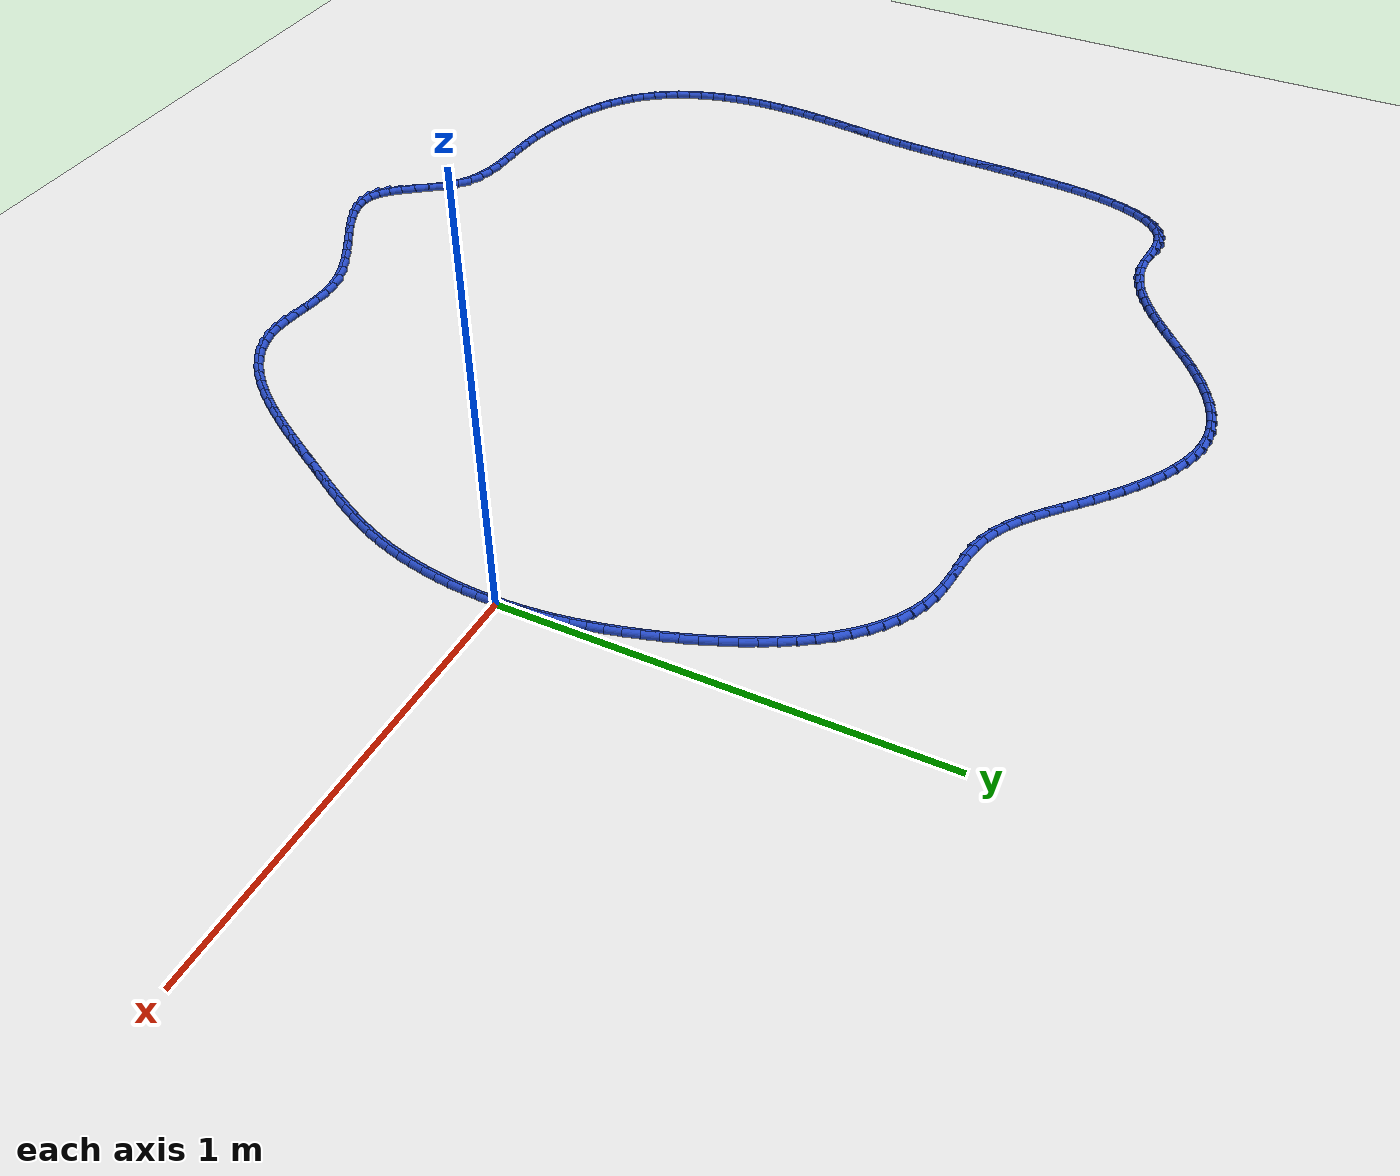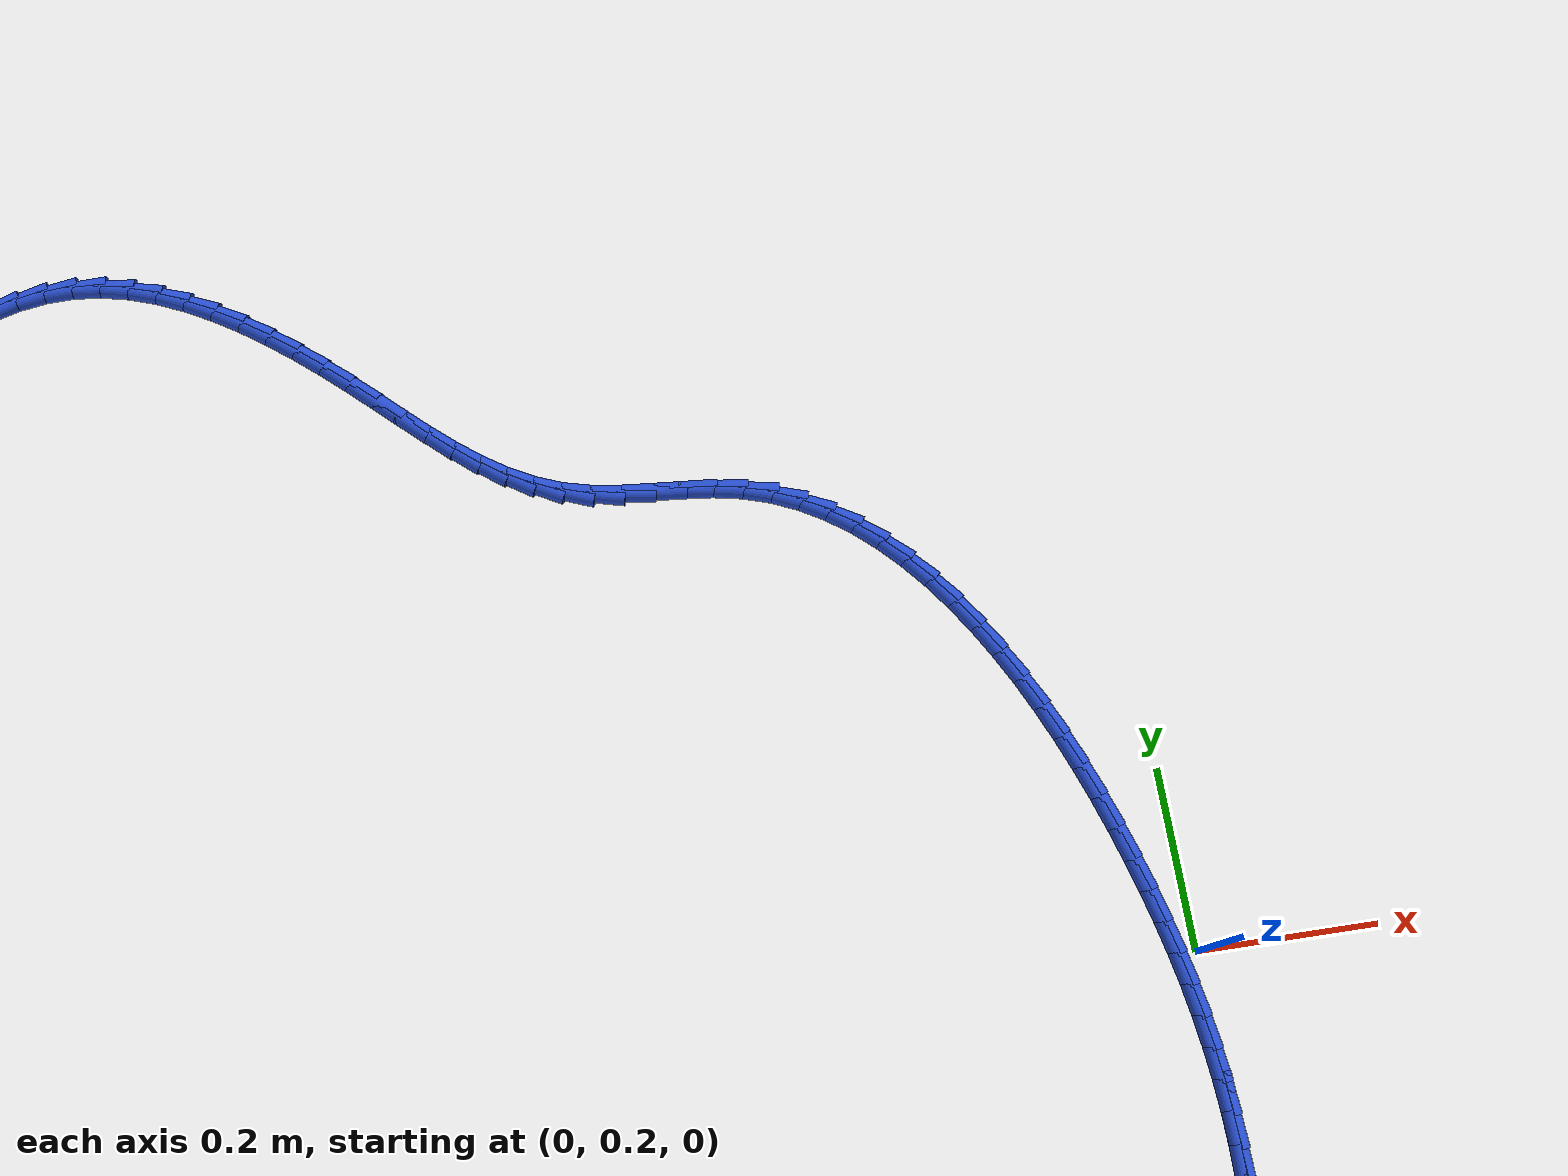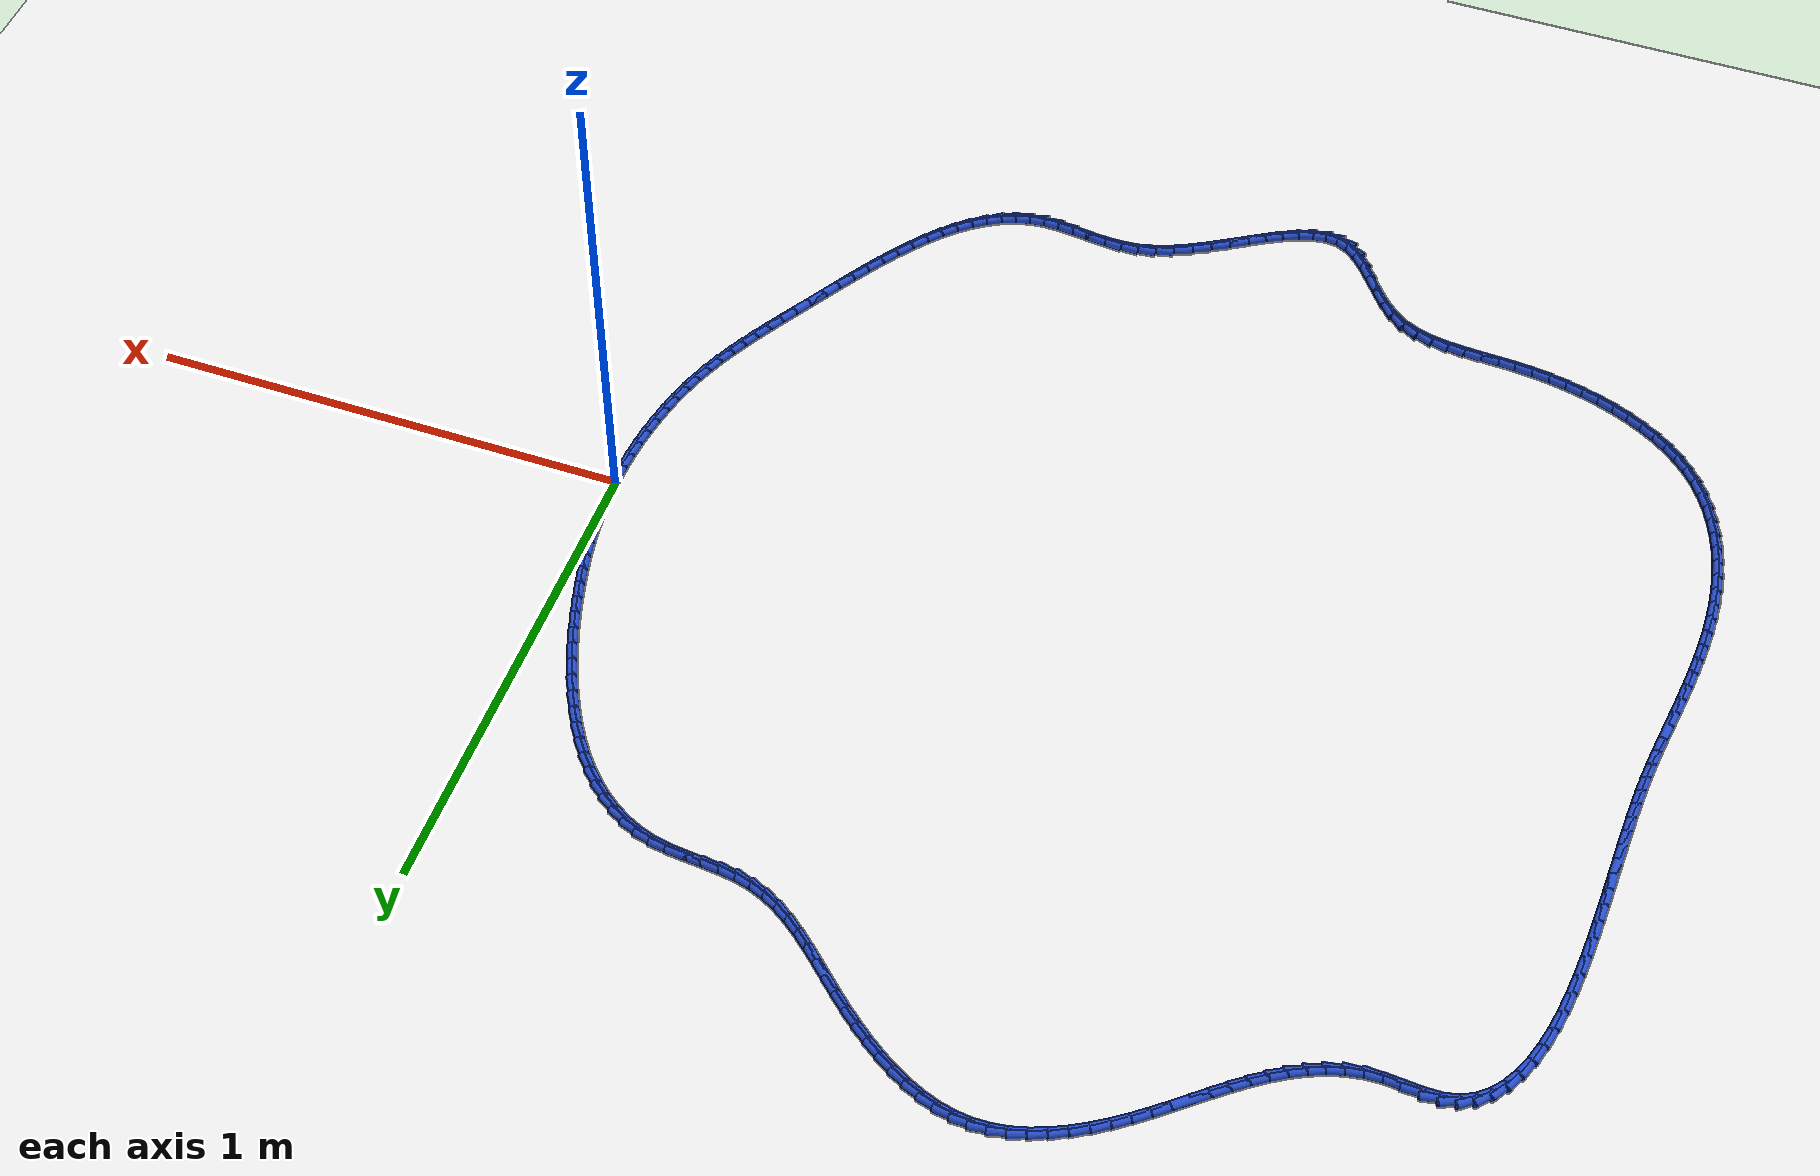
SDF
<sdf version="1.6">
 <world name="default">
  <light name="sun" type="directional">
   <pose>0 0 10 0 -0 0</pose>
   <diffuse>0.8 0.8 0.8 1</diffuse>
   <specular>0.2 0.2 0.2 1</specular>
   <attenuation>
    <range>1000</range>
    <constant>0.9</constant>
    <linear>0.01</linear>
    <quadratic>0.001</quadratic>
   </attenuation>
   <direction>-0.5 0.1 -0.9</direction>
  </light>
  <model name="ground_plane">
   <static>1</static>
   <link name="link">
    <collision name="collision">
     <geometry><plane><normal>0 0 1</normal><size>100 100</size></plane></geometry>
     <surface><friction><ode><mu>100</mu><mu2>50</mu2></ode></friction></surface>
    </collision>
    <visual name="visual">
     <cast_shadows>0</cast_shadows>
     <geometry><plane><normal>0 0 1</normal><size>100 100</size></plane></geometry>
     <material>
      <script><uri>file://media/materials/scripts/gazebo.material</uri><name>Gazebo/WhiteGlow</name></script>
     </material>
    </visual>
   </link>
  </model>
  <gravity>0 0 -9.8</gravity>
  <magnetic_field>6e-06 2.3e-05 -4.2e-05</magnetic_field>
  <atmosphere type="adiabatic"/>
  <physics name="default_physics" default="0" type="ode">
   <max_step_size>0.001</max_step_size>
   <real_time_factor>1</real_time_factor>
   <real_time_update_rate>1000</real_time_update_rate>
  </physics>
  <scene><ambient>0.4 0.4 0.4 1</ambient><background>0.7 0.7 0.7 1</background><shadows>1</shadows></scene>
  <spherical_coordinates>
   <surface_model>EARTH_WGS84</surface_model>
   <latitude_deg>0</latitude_deg>
   <longitude_deg>0</longitude_deg>
   <elevation>0</elevation>
   <heading_deg>0</heading_deg>
  </spherical_coordinates>
  <model name="line">
   <link name="link_0">
    <pose>1.5612511283791264e-17 -6.938893903907228e-17 0.01 0 1.57 -1.5468301121806811</pose>
    <collision name="collision">
     <geometry><cylinder><radius>0.01</radius><length>0.08</length></cylinder></geometry>
    </collision>
    <visual name="visual">
     <material>
      <script><name>Gazebo/Blue</name><uri>file://media/materials/scripts/gazebo.material</uri></script>
     </material>
     <geometry><cylinder><radius>0.01</radius><length>0.08</length></cylinder></geometry>
    </visual>
   </link>
   <link name="link_1">
    <pose>-0.0008232692903801181 0.034344667049356056 0.01 0 1.57 -1.5116238401497004</pose>
    <collision name="collision">
     <geometry><cylinder><radius>0.01</radius><length>0.08</length></cylinder></geometry>
    </collision>
    <visual name="visual">
     <material>
      <script><name>Gazebo/Blue</name><uri>file://media/materials/scripts/gazebo.material</uri></script>
     </material>
     <geometry><cylinder><radius>0.01</radius><length>0.08</length></cylinder></geometry>
    </visual>
   </link>
   <link name="link_2">
    <pose>-0.0028426408338338882 0.0684316936888838 0.01 0 1.57 -1.4769170290811109</pose>
    <collision name="collision">
     <geometry><cylinder><radius>0.01</radius><length>0.08</length></cylinder></geometry>
    </collision>
    <visual name="visual">
     <material>
      <script><name>Gazebo/Blue</name><uri>file://media/materials/scripts/gazebo.material</uri></script>
     </material>
     <geometry><cylinder><radius>0.01</radius><length>0.08</length></cylinder></geometry>
    </visual>
   </link>
   <link name="link_3">
    <pose>-0.006037344235162098 0.10236156579821623 0.01 0 1.57 -1.4430966344124054</pose>
    <collision name="collision">
     <geometry><cylinder><radius>0.01</radius><length>0.08</length></cylinder></geometry>
    </collision>
    <visual name="visual">
     <material>
      <script><name>Gazebo/Blue</name><uri>file://media/materials/scripts/gazebo.material</uri></script>
     </material>
     <geometry><cylinder><radius>0.01</radius><length>0.08</length></cylinder></geometry>
    </visual>
   </link>
   <link name="link_4">
    <pose>-0.010386609099165552 0.13623476925698658 0.01 0 1.57 -1.4105220477981952</pose>
    <collision name="collision">
     <geometry><cylinder><radius>0.01</radius><length>0.08</length></cylinder></geometry>
    </collision>
    <visual name="visual">
     <material>
      <script><name>Gazebo/Blue</name><uri>file://media/materials/scripts/gazebo.material</uri></script>
     </material>
     <geometry><cylinder><radius>0.01</radius><length>0.08</length></cylinder></geometry>
    </visual>
   </link>
   <link name="link_5">
    <pose>-0.01586966503064504 0.17015178994482788 0.01 0 1.57 -1.3795110600730716</pose>
    <collision name="collision">
     <geometry><cylinder><radius>0.01</radius><length>0.08</length></cylinder></geometry>
    </collision>
    <visual name="visual">
     <material>
      <script><name>Gazebo/Blue</name><uri>file://media/materials/scripts/gazebo.material</uri></script>
     </material>
     <geometry><cylinder><radius>0.01</radius><length>0.08</length></cylinder></geometry>
    </visual>
   </link>
   <link name="link_6">
    <pose>-0.02246574163440137 0.20421311374137338 0.01 0 1.57 -1.3503296061707348</pose>
    <collision name="collision">
     <geometry><cylinder><radius>0.01</radius><length>0.08</length></cylinder></geometry>
    </collision>
    <visual name="visual">
     <material>
      <script><name>Gazebo/Blue</name><uri>file://media/materials/scripts/gazebo.material</uri></script>
     </material>
     <geometry><cylinder><radius>0.01</radius><length>0.08</length></cylinder></geometry>
    </visual>
   </link>
   <link name="link_7">
    <pose>-0.030154068515235354 0.2385192265262563 0.01 0 1.57 -1.323185847687289</pose>
    <collision name="collision">
     <geometry><cylinder><radius>0.01</radius><length>0.08</length></cylinder></geometry>
    </collision>
    <visual name="visual">
     <material>
      <script><name>Gazebo/Blue</name><uri>file://media/materials/scripts/gazebo.material</uri></script>
     </material>
     <geometry><cylinder><radius>0.01</radius><length>0.08</length></cylinder></geometry>
    </visual>
   </link>
   <link name="link_8">
    <pose>-0.038913875277947756 0.27317061417910954 0.01 0 1.57 -1.298228519508676</pose>
    <collision name="collision">
     <geometry><cylinder><radius>0.01</radius><length>0.08</length></cylinder></geometry>
    </collision>
    <visual name="visual">
     <material>
      <script><name>Gazebo/Blue</name><uri>file://media/materials/scripts/gazebo.material</uri></script>
     </material>
     <geometry><cylinder><radius>0.01</radius><length>0.08</length></cylinder></geometry>
    </visual>
   </link>
   <link name="link_9">
    <pose>-0.04872439152733941 0.30826776257956645 0.01 0 1.57 -1.2748941390368624</pose>
    <collision name="collision">
     <geometry><cylinder><radius>0.01</radius><length>0.08</length></cylinder></geometry>
    </collision>
    <visual name="visual">
     <material>
      <script><name>Gazebo/Blue</name><uri>file://media/materials/scripts/gazebo.material</uri></script>
     </material>
     <geometry><cylinder><radius>0.01</radius><length>0.08</length></cylinder></geometry>
    </visual>
   </link>
   <link name="link_10">
    <pose>-0.05957353465155941 0.3438559948654001 0.01 0 1.57 -1.2503113816151594</pose>
    <collision name="collision">
     <geometry><cylinder><radius>0.01</radius><length>0.08</length></cylinder></geometry>
    </collision>
    <visual name="visual">
     <material>
      <script><name>Gazebo/Blue</name><uri>file://media/materials/scripts/gazebo.material</uri></script>
     </material>
     <geometry><cylinder><radius>0.01</radius><length>0.08</length></cylinder></geometry>
    </visual>
   </link>
   <link name="link_11">
    <pose>-0.0714862545436593 0.3797454977274361 0.01 0 1.57 -1.2234359088546058</pose>
    <collision name="collision">
     <geometry><cylinder><radius>0.01</radius><length>0.08</length></cylinder></geometry>
    </collision>
    <visual name="visual">
     <material>
      <script><name>Gazebo/Blue</name><uri>file://media/materials/scripts/gazebo.material</uri></script>
     </material>
     <geometry><cylinder><radius>0.01</radius><length>0.08</length></cylinder></geometry>
    </visual>
   </link>
   <link name="link_12">
    <pose>-0.08449736651621093 0.41568381775965096 0.01 0 1.57 -1.1939030078868191</pose>
    <collision name="collision">
     <geometry><cylinder><radius>0.01</radius><length>0.08</length></cylinder></geometry>
    </collision>
    <visual name="visual">
     <material>
      <script><name>Gazebo/Blue</name><uri>file://media/materials/scripts/gazebo.material</uri></script>
     </material>
     <geometry><cylinder><radius>0.01</radius><length>0.08</length></cylinder></geometry>
    </visual>
   </link>
   <link name="link_13">
    <pose>-0.09864168596992146 0.4514185009964106 0.01 0 1.57 -1.161293176589283</pose>
    <collision name="collision">
     <geometry><cylinder><radius>0.01</radius><length>0.08</length></cylinder></geometry>
    </collision>
    <visual name="visual">
     <material>
      <script><name>Gazebo/Blue</name><uri>file://media/materials/scripts/gazebo.material</uri></script>
     </material>
     <geometry><cylinder><radius>0.01</radius><length>0.08</length></cylinder></geometry>
    </visual>
   </link>
   <link name="link_14">
    <pose>-0.1139540283054979 0.48669709347208023 0.01 0 1.57 -1.125122166517232</pose>
    <collision name="collision">
     <geometry><cylinder><radius>0.01</radius><length>0.08</length></cylinder></geometry>
    </collision>
    <visual name="visual">
     <material>
      <script><name>Gazebo/Blue</name><uri>file://media/materials/scripts/gazebo.material</uri></script>
     </material>
     <geometry><cylinder><radius>0.01</radius><length>0.08</length></cylinder></geometry>
    </visual>
   </link>
   <link name="link_15">
    <pose>-0.13046920892364738 0.5212671412210256 0.01 0 1.57 -1.0848316193505072</pose>
    <collision name="collision">
     <geometry><cylinder><radius>0.01</radius><length>0.08</length></cylinder></geometry>
    </collision>
    <visual name="visual">
     <material>
      <script><name>Gazebo/Blue</name><uri>file://media/materials/scripts/gazebo.material</uri></script>
     </material>
     <geometry><cylinder><radius>0.01</radius><length>0.08</length></cylinder></geometry>
    </visual>
   </link>
   <link name="link_16">
    <pose>-0.14822204322507704 0.5548761902776121 0.01 0 1.57 -1.0397818706488213</pose>
    <collision name="collision">
     <geometry><cylinder><radius>0.01</radius><length>0.08</length></cylinder></geometry>
    </collision>
    <visual name="visual">
     <material>
      <script><name>Gazebo/Blue</name><uri>file://media/materials/scripts/gazebo.material</uri></script>
     </material>
     <geometry><cylinder><radius>0.01</radius><length>0.08</length></cylinder></geometry>
    </visual>
   </link>
   <link name="link_17">
    <pose>-0.16724734661049392 0.5872717866762054 0.01 0 1.57 -0.9892498983041441</pose>
    <collision name="collision">
     <geometry><cylinder><radius>0.01</radius><length>0.08</length></cylinder></geometry>
    </collision>
    <visual name="visual">
     <material>
      <script><name>Gazebo/Blue</name><uri>file://media/materials/scripts/gazebo.material</uri></script>
     </material>
     <geometry><cylinder><radius>0.01</radius><length>0.08</length></cylinder></geometry>
    </visual>
   </link>
   <link name="link_18">
    <pose>-0.187579934480605 0.6182014764511705 0.01 0 1.57 -0.9324375255819655</pose>
    <collision name="collision">
     <geometry><cylinder><radius>0.01</radius><length>0.08</length></cylinder></geometry>
    </collision>
    <visual name="visual">
     <material>
      <script><name>Gazebo/Blue</name><uri>file://media/materials/scripts/gazebo.material</uri></script>
     </material>
     <geometry><cylinder><radius>0.01</radius><length>0.08</length></cylinder></geometry>
    </visual>
   </link>
   <link name="link_19">
    <pose>-0.2092546222361176 0.6474128056368738 0.01 0 1.57 -0.8684979622804968</pose>
    <collision name="collision">
     <geometry><cylinder><radius>0.01</radius><length>0.08</length></cylinder></geometry>
    </collision>
    <visual name="visual">
     <material>
      <script><name>Gazebo/Blue</name><uri>file://media/materials/scripts/gazebo.material</uri></script>
     </material>
     <geometry><cylinder><radius>0.01</radius><length>0.08</length></cylinder></geometry>
    </visual>
   </link>
   <link name="link_20">
    <pose>-0.23230622527773873 0.6746533202676802 0.01 0 1.57 -0.7965922368507615</pose>
    <collision name="collision">
     <geometry><cylinder><radius>0.01</radius><length>0.08</length></cylinder></geometry>
    </collision>
    <visual name="visual">
     <material>
      <script><name>Gazebo/Blue</name><uri>file://media/materials/scripts/gazebo.material</uri></script>
     </material>
     <geometry><cylinder><radius>0.01</radius><length>0.08</length></cylinder></geometry>
    </visual>
   </link>
   <link name="link_21">
    <pose>-0.2567695590061753 0.6996705663779552 0.01 0 1.57 -0.7159895367759453</pose>
    <collision name="collision">
     <geometry><cylinder><radius>0.01</radius><length>0.08</length></cylinder></geometry>
    </collision>
    <visual name="visual">
     <material>
      <script><name>Gazebo/Blue</name><uri>file://media/materials/scripts/gazebo.material</uri></script>
     </material>
     <geometry><cylinder><radius>0.01</radius><length>0.08</length></cylinder></geometry>
    </visual>
   </link>
   <link name="link_22">
    <pose>-0.28267943882213464 0.7222120900020648 0.01 0 1.57 -0.6262232501258135</pose>
    <collision name="collision">
     <geometry><cylinder><radius>0.01</radius><length>0.08</length></cylinder></geometry>
    </collision>
    <visual name="visual">
     <material>
      <script><name>Gazebo/Blue</name><uri>file://media/materials/scripts/gazebo.material</uri></script>
     </material>
     <geometry><cylinder><radius>0.01</radius><length>0.08</length></cylinder></geometry>
    </visual>
   </link>
   <link name="link_23">
    <pose>-0.3100706801263239 0.7420254371743742 0.01 0 1.57 -0.5273012350060815</pose>
    <collision name="collision">
     <geometry><cylinder><radius>0.01</radius><length>0.08</length></cylinder></geometry>
    </collision>
    <visual name="visual">
     <material>
      <script><name>Gazebo/Blue</name><uri>file://media/materials/scripts/gazebo.material</uri></script>
     </material>
     <geometry><cylinder><radius>0.01</radius><length>0.08</length></cylinder></geometry>
    </visual>
   </link>
   <link name="link_24">
    <pose>-0.3389780983194499 0.7588581539292493 0.01 0 1.57 -0.41993820278258054</pose>
    <collision name="collision">
     <geometry><cylinder><radius>0.01</radius><length>0.08</length></cylinder></geometry>
    </collision>
    <visual name="visual">
     <material>
      <script><name>Gazebo/Blue</name><uri>file://media/materials/scripts/gazebo.material</uri></script>
     </material>
     <geometry><cylinder><radius>0.01</radius><length>0.08</length></cylinder></geometry>
    </visual>
   </link>
   <link name="link_25">
    <pose>-0.3694365088022198 0.7724577863010549 0.01 0 1.57 -0.30573321195760766</pose>
    <collision name="collision">
     <geometry><cylinder><radius>0.01</radius><length>0.08</length></cylinder></geometry>
    </collision>
    <visual name="visual">
     <material>
      <script><name>Gazebo/Blue</name><uri>file://media/materials/scripts/gazebo.material</uri></script>
     </material>
     <geometry><cylinder><radius>0.01</radius><length>0.08</length></cylinder></geometry>
    </visual>
   </link>
   <link name="link_26">
    <pose>-0.4014807269753409 0.7825718803241573 0.01 0 1.57 -0.19208338854878154</pose>
    <collision name="collision">
     <geometry><cylinder><radius>0.01</radius><length>0.08</length></cylinder></geometry>
    </collision>
    <visual name="visual">
     <material>
      <script><name>Gazebo/Blue</name><uri>file://media/materials/scripts/gazebo.material</uri></script>
     </material>
     <geometry><cylinder><radius>0.01</radius><length>0.08</length></cylinder></geometry>
    </visual>
   </link>
   <link name="link_27">
    <pose>-0.43508282652247965 0.7891068553989355 0.01 0 1.57 -0.11354272169219927</pose>
    <collision name="collision">
     <geometry><cylinder><radius>0.01</radius><length>0.08</length></cylinder></geometry>
    </collision>
    <visual name="visual">
     <material>
      <script><name>Gazebo/Blue</name><uri>file://media/materials/scripts/gazebo.material</uri></script>
     </material>
     <geometry><cylinder><radius>0.01</radius><length>0.08</length></cylinder></geometry>
    </visual>
   </link>
   <link name="link_28">
    <pose>-0.46978258637481884 0.793063779361882 0.01 0 1.57 -0.08064058281410354</pose>
    <collision name="collision">
     <geometry><cylinder><radius>0.01</radius><length>0.08</length></cylinder></geometry>
    </collision>
    <visual name="visual">
     <material>
      <script><name>Gazebo/Blue</name><uri>file://media/materials/scripts/gazebo.material</uri></script>
     </material>
     <geometry><cylinder><radius>0.01</radius><length>0.08</length></cylinder></geometry>
    </visual>
   </link>
   <link name="link_29">
    <pose>-0.5049376709220021 0.7959048669797794 0.01 0 1.57 -0.09094979658502232</pose>
    <collision name="collision">
     <geometry><cylinder><radius>0.01</radius><length>0.08</length></cylinder></geometry>
    </collision>
    <visual name="visual">
     <material>
      <script><name>Gazebo/Blue</name><uri>file://media/materials/scripts/gazebo.material</uri></script>
     </material>
     <geometry><cylinder><radius>0.01</radius><length>0.08</length></cylinder></geometry>
    </visual>
   </link>
   <link name="link_30">
    <pose>-0.5399051074489903 0.799093946283605 0.01 0 1.57 -0.14546107586776216</pose>
    <collision name="collision">
     <geometry><cylinder><radius>0.01</radius><length>0.08</length></cylinder></geometry>
    </collision>
    <visual name="visual">
     <material>
      <script><name>Gazebo/Blue</name><uri>file://media/materials/scripts/gazebo.material</uri></script>
     </material>
     <geometry><cylinder><radius>0.01</radius><length>0.08</length></cylinder></geometry>
    </visual>
   </link>
   <link name="link_31">
    <pose>-0.574041923240744 0.8040948453043358 0.01 0 1.57 -0.2477213466140488</pose>
    <collision name="collision">
     <geometry><cylinder><radius>0.01</radius><length>0.08</length></cylinder></geometry>
    </collision>
    <visual name="visual">
     <material>
      <script><name>Gazebo/Blue</name><uri>file://media/materials/scripts/gazebo.material</uri></script>
     </material>
     <geometry><cylinder><radius>0.01</radius><length>0.08</length></cylinder></geometry>
    </visual>
   </link>
   <link name="link_32">
    <pose>-0.6067117567632987 0.8123575724481106 0.01 0 1.57 -0.37602174688956047</pose>
    <collision name="collision">
     <geometry><cylinder><radius>0.01</radius><length>0.08</length></cylinder></geometry>
    </collision>
    <visual name="visual">
     <material>
      <script><name>Gazebo/Blue</name><uri>file://media/materials/scripts/gazebo.material</uri></script>
     </material>
     <geometry><cylinder><radius>0.01</radius><length>0.08</length></cylinder></geometry>
    </visual>
   </link>
   <link name="link_33">
    <pose>-0.6376430923885111 0.8245694836563725 0.01 0 1.57 -0.4895912701656224</pose>
    <collision name="collision">
     <geometry><cylinder><radius>0.01</radius><length>0.08</length></cylinder></geometry>
    </collision>
    <visual name="visual">
     <material>
      <script><name>Gazebo/Blue</name><uri>file://media/materials/scripts/gazebo.material</uri></script>
     </material>
     <geometry><cylinder><radius>0.01</radius><length>0.08</length></cylinder></geometry>
    </visual>
   </link>
   <link name="link_34">
    <pose>-0.6671123479816877 0.8402725668601148 0.01 0 1.57 -0.5820176094985772</pose>
    <collision name="collision">
     <geometry><cylinder><radius>0.01</radius><length>0.08</length></cylinder></geometry>
    </collision>
    <visual name="visual">
     <material>
      <script><name>Gazebo/Blue</name><uri>file://media/materials/scripts/gazebo.material</uri></script>
     </material>
     <geometry><cylinder><radius>0.01</radius><length>0.08</length></cylinder></geometry>
    </visual>
   </link>
   <link name="link_35">
    <pose>-0.6954410792702869 0.8589144564529277 0.01 0 1.57 -0.6526505553294145</pose>
    <collision name="collision">
     <geometry><cylinder><radius>0.01</radius><length>0.08</length></cylinder></geometry>
    </collision>
    <visual name="visual">
     <material>
      <script><name>Gazebo/Blue</name><uri>file://media/materials/scripts/gazebo.material</uri></script>
     </material>
     <geometry><cylinder><radius>0.01</radius><length>0.08</length></cylinder></geometry>
    </visual>
   </link>
   <link name="link_36">
    <pose>-0.7229508419817668 0.8799427868284014 0.01 0 1.57 -0.70238208552265</pose>
    <collision name="collision">
     <geometry><cylinder><radius>0.01</radius><length>0.08</length></cylinder></geometry>
    </collision>
    <visual name="visual">
     <material>
      <script><name>Gazebo/Blue</name><uri>file://media/materials/scripts/gazebo.material</uri></script>
     </material>
     <geometry><cylinder><radius>0.01</radius><length>0.08</length></cylinder></geometry>
    </visual>
   </link>
   <link name="link_37">
    <pose>-0.7499631918435862 0.9028051923801266 0.01 0 1.57 -0.7326353812267159</pose>
    <collision name="collision">
     <geometry><cylinder><radius>0.01</radius><length>0.08</length></cylinder></geometry>
    </collision>
    <visual name="visual">
     <material>
      <script><name>Gazebo/Blue</name><uri>file://media/materials/scripts/gazebo.material</uri></script>
     </material>
     <geometry><cylinder><radius>0.01</radius><length>0.08</length></cylinder></geometry>
    </visual>
   </link>
   <link name="link_38">
    <pose>-0.776799684583203 0.926949307501693 0.01 0 1.57 -0.744755128222772</pose>
    <collision name="collision">
     <geometry><cylinder><radius>0.01</radius><length>0.08</length></cylinder></geometry>
    </collision>
    <visual name="visual">
     <material>
      <script><name>Gazebo/Blue</name><uri>file://media/materials/scripts/gazebo.material</uri></script>
     </material>
     <geometry><cylinder><radius>0.01</radius><length>0.08</length></cylinder></geometry>
    </visual>
   </link>
   <link name="link_39">
    <pose>-0.8037818759280755 0.951822766586691 0.01 0 1.57 -0.7397344321750668</pose>
    <collision name="collision">
     <geometry><cylinder><radius>0.01</radius><length>0.08</length></cylinder></geometry>
    </collision>
    <visual name="visual">
     <material>
      <script><name>Gazebo/Blue</name><uri>file://media/materials/scripts/gazebo.material</uri></script>
     </material>
     <geometry><cylinder><radius>0.01</radius><length>0.08</length></cylinder></geometry>
    </visual>
   </link>
   <link name="link_40">
    <pose>-0.8312313216056625 0.9768732040287116 0.01 0 1.57 -0.7194864768363495</pose>
    <collision name="collision">
     <geometry><cylinder><radius>0.01</radius><length>0.08</length></cylinder></geometry>
    </collision>
    <visual name="visual">
     <material>
      <script><name>Gazebo/Blue</name><uri>file://media/materials/scripts/gazebo.material</uri></script>
     </material>
     <geometry><cylinder><radius>0.01</radius><length>0.08</length></cylinder></geometry>
    </visual>
   </link>
   <link name="link_41">
    <pose>-0.8594181808605208 1.001569395838576 0.01 0 1.57 -0.6905855351061072</pose>
    <collision name="collision">
     <geometry><cylinder><radius>0.01</radius><length>0.08</length></cylinder></geometry>
    </collision>
    <visual name="visual">
     <material>
      <script><name>Gazebo/Blue</name><uri>file://media/materials/scripts/gazebo.material</uri></script>
     </material>
     <geometry><cylinder><radius>0.01</radius><length>0.08</length></cylinder></geometry>
    </visual>
   </link>
   <link name="link_42">
    <pose>-0.8883595158805042 1.025484227895982 0.01 0 1.57 -0.6544674693889861</pose>
    <collision name="collision">
     <geometry><cylinder><radius>0.01</radius><length>0.08</length></cylinder></geometry>
    </collision>
    <visual name="visual">
     <material>
      <script><name>Gazebo/Blue</name><uri>file://media/materials/scripts/gazebo.material</uri></script>
     </material>
     <geometry><cylinder><radius>0.01</radius><length>0.08</length></cylinder></geometry>
    </visual>
   </link>
   <link name="link_43">
    <pose>-0.9179946134673654 1.048222578492366 0.01 0 1.57 -0.6102616828663859</pose>
    <collision name="collision">
     <geometry><cylinder><radius>0.01</radius><length>0.08</length></cylinder></geometry>
    </collision>
    <visual name="visual">
     <material>
      <script><name>Gazebo/Blue</name><uri>file://media/materials/scripts/gazebo.material</uri></script>
     </material>
     <geometry><cylinder><radius>0.01</radius><length>0.08</length></cylinder></geometry>
    </visual>
   </link>
   <link name="link_44">
    <pose>-0.9482627393894696 1.069389334571117 0.01 0 1.57 -0.5568436397219181</pose>
    <collision name="collision">
     <geometry><cylinder><radius>0.01</radius><length>0.08</length></cylinder></geometry>
    </collision>
    <visual name="visual">
     <material>
      <script><name>Gazebo/Blue</name><uri>file://media/materials/scripts/gazebo.material</uri></script>
     </material>
     <geometry><cylinder><radius>0.01</radius><length>0.08</length></cylinder></geometry>
    </visual>
   </link>
   <link name="link_45">
    <pose>-0.9791031594151814 1.088589383075623 0.01 0 1.57 -0.4928624767347544</pose>
    <collision name="collision">
     <geometry><cylinder><radius>0.01</radius><length>0.08</length></cylinder></geometry>
    </collision>
    <visual name="visual">
     <material>
      <script><name>Gazebo/Blue</name><uri>file://media/materials/scripts/gazebo.material</uri></script>
     </material>
     <geometry><cylinder><radius>0.01</radius><length>0.08</length></cylinder></geometry>
    </visual>
   </link>
   <link name="link_46">
    <pose>-1.0104551393128658 1.1054276109492724 0.01 0 1.57 -0.41682431916936086</pose>
    <collision name="collision">
     <geometry><cylinder><radius>0.01</radius><length>0.08</length></cylinder></geometry>
    </collision>
    <visual name="visual">
     <material>
      <script><name>Gazebo/Blue</name><uri>file://media/materials/scripts/gazebo.material</uri></script>
     </material>
     <geometry><cylinder><radius>0.01</radius><length>0.08</length></cylinder></geometry>
    </visual>
   </link>
   <link name="link_47">
    <pose>-1.0422579448508873 1.1195089051354539 0.01 0 1.57 -0.32728353474115207</pose>
    <collision name="collision">
     <geometry><cylinder><radius>0.01</radius><length>0.08</length></cylinder></geometry>
    </collision>
    <visual name="visual">
     <material>
      <script><name>Gazebo/Blue</name><uri>file://media/materials/scripts/gazebo.material</uri></script>
     </material>
     <geometry><cylinder><radius>0.01</radius><length>0.08</length></cylinder></geometry>
    </visual>
   </link>
   <link name="link_48">
    <pose>-1.0744508417976113 1.1304381525775553 0.01 0 1.57 -0.22320368448068828</pose>
    <collision name="collision">
     <geometry><cylinder><radius>0.01</radius><length>0.08</length></cylinder></geometry>
    </collision>
    <visual name="visual">
     <material>
      <script><name>Gazebo/Blue</name><uri>file://media/materials/scripts/gazebo.material</uri></script>
     </material>
     <geometry><cylinder><radius>0.01</radius><length>0.08</length></cylinder></geometry>
    </visual>
   </link>
   <link name="link_49">
    <pose>-1.1069730959214021 1.1378202402189652 0.01 0 1.57 -0.1045193089795949</pose>
    <collision name="collision">
     <geometry><cylinder><radius>0.01</radius><length>0.08</length></cylinder></geometry>
    </collision>
    <visual name="visual">
     <material>
      <script><name>Gazebo/Blue</name><uri>file://media/materials/scripts/gazebo.material</uri></script>
     </material>
     <geometry><cylinder><radius>0.01</radius><length>0.08</length></cylinder></geometry>
    </visual>
   </link>
   <link name="link_50">
    <pose>-1.1397639729906248 1.1412600550030723 0.01 0 1.57 0.026673547883761722</pose>
    <collision name="collision">
     <geometry><cylinder><radius>0.01</radius><length>0.08</length></cylinder></geometry>
    </collision>
    <visual name="visual">
     <material>
      <script><name>Gazebo/Blue</name><uri>file://media/materials/scripts/gazebo.material</uri></script>
     </material>
     <geometry><cylinder><radius>0.01</radius><length>0.08</length></cylinder></geometry>
    </visual>
   </link>
   <link name="link_51">
    <pose>-1.1727604223580879 1.1403797138398022 0.01 0 1.57 0.1551874849162327</pose>
    <collision name="collision">
     <geometry><cylinder><radius>0.01</radius><length>0.08</length></cylinder></geometry>
    </collision>
    <visual name="visual">
     <material>
      <script><name>Gazebo/Blue</name><uri>file://media/materials/scripts/gazebo.material</uri></script>
     </material>
     <geometry><cylinder><radius>0.01</radius><length>0.08</length></cylinder></geometry>
    </visual>
   </link>
   <link name="link_52">
    <pose>-1.20584529373193 1.1352037377175122 0.01 0 1.57 0.267403179976876</pose>
    <collision name="collision">
     <geometry><cylinder><radius>0.01</radius><length>0.08</length></cylinder></geometry>
    </collision>
    <visual name="visual">
     <material>
      <script><name>Gazebo/Blue</name><uri>file://media/materials/scripts/gazebo.material</uri></script>
     </material>
     <geometry><cylinder><radius>0.01</radius><length>0.08</length></cylinder></geometry>
    </visual>
   </link>
   <link name="link_53">
    <pose>-1.2388468764806124 1.1261624784454707 0.01 0 1.57 0.3635602836979531</pose>
    <collision name="collision">
     <geometry><cylinder><radius>0.01</radius><length>0.08</length></cylinder></geometry>
    </collision>
    <visual name="visual">
     <material>
      <script><name>Gazebo/Blue</name><uri>file://media/materials/scripts/gazebo.material</uri></script>
     </material>
     <geometry><cylinder><radius>0.01</radius><length>0.08</length></cylinder></geometry>
    </visual>
   </link>
   <link name="link_54">
    <pose>-1.2715910514159616 1.1137042031634286 0.01 0 1.57 0.4454290458438311</pose>
    <collision name="collision">
     <geometry><cylinder><radius>0.01</radius><length>0.08</length></cylinder></geometry>
    </collision>
    <visual name="visual">
     <material>
      <script><name>Gazebo/Blue</name><uri>file://media/materials/scripts/gazebo.material</uri></script>
     </material>
     <geometry><cylinder><radius>0.01</radius><length>0.08</length></cylinder></geometry>
    </visual>
   </link>
   <link name="link_55">
    <pose>-1.3039036993498028 1.0982771790111363 0.01 0 1.57 0.5150763140110858</pose>
    <collision name="collision">
     <geometry><cylinder><radius>0.01</radius><length>0.08</length></cylinder></geometry>
    </collision>
    <visual name="visual">
     <material>
      <script><name>Gazebo/Blue</name><uri>file://media/materials/scripts/gazebo.material</uri></script>
     </material>
     <geometry><cylinder><radius>0.01</radius><length>0.08</length></cylinder></geometry>
    </visual>
   </link>
   <link name="link_56">
    <pose>-1.3356107010939628 1.0803296731283443 0.01 0 1.57 0.5744866688696507</pose>
    <collision name="collision">
     <geometry><cylinder><radius>0.01</radius><length>0.08</length></cylinder></geometry>
    </collision>
    <visual name="visual">
     <material>
      <script><name>Gazebo/Blue</name><uri>file://media/materials/scripts/gazebo.material</uri></script>
     </material>
     <geometry><cylinder><radius>0.01</radius><length>0.08</length></cylinder></geometry>
    </visual>
   </link>
   <link name="link_57">
    <pose>-1.3665379374602666 1.0603099526548025 0.01 0 1.57 0.6245268697723203</pose>
    <collision name="collision">
     <geometry><cylinder><radius>0.01</radius><length>0.08</length></cylinder></geometry>
    </collision>
    <visual name="visual">
     <material>
      <script><name>Gazebo/Blue</name><uri>file://media/materials/scripts/gazebo.material</uri></script>
     </material>
     <geometry><cylinder><radius>0.01</radius><length>0.08</length></cylinder></geometry>
    </visual>
   </link>
   <link name="link_58">
    <pose>-1.3965663846158385 1.0386664907402936 0.01 0 1.57 0.6624686107490294</pose>
    <collision name="collision">
     <geometry><cylinder><radius>0.01</radius><length>0.08</length></cylinder></geometry>
    </collision>
    <visual name="visual">
     <material>
      <script><name>Gazebo/Blue</name><uri>file://media/materials/scripts/gazebo.material</uri></script>
     </material>
     <geometry><cylinder><radius>0.01</radius><length>0.08</length></cylinder></geometry>
    </visual>
   </link>
   <link name="link_59">
    <pose>-1.4258174617749397 1.0158486595882337 0.01 0 1.57 0.6876684319064283</pose>
    <collision name="collision">
     <geometry><cylinder><radius>0.01</radius><length>0.08</length></cylinder></geometry>
    </collision>
    <visual name="visual">
     <material>
      <script><name>Gazebo/Blue</name><uri>file://media/materials/scripts/gazebo.material</uri></script>
     </material>
     <geometry><cylinder><radius>0.01</radius><length>0.08</length></cylinder></geometry>
    </visual>
   </link>
   <link name="link_60">
    <pose>-1.4544781626176728 0.9923060765950814 0.01 0 1.57 0.700349872848453</pose>
    <collision name="collision">
     <geometry><cylinder><radius>0.01</radius><length>0.08</length></cylinder></geometry>
    </collision>
    <visual name="visual">
     <material>
      <script><name>Gazebo/Blue</name><uri>file://media/materials/scripts/gazebo.material</uri></script>
     </material>
     <geometry><cylinder><radius>0.01</radius><length>0.08</length></cylinder></geometry>
    </visual>
   </link>
   <link name="link_61">
    <pose>-1.4827354822961087 0.9684883591628003 0.01 0 1.57 0.7005146841830622</pose>
    <collision name="collision">
     <geometry><cylinder><radius>0.01</radius><length>0.08</length></cylinder></geometry>
    </collision>
    <visual name="visual">
     <material>
      <script><name>Gazebo/Blue</name><uri>file://media/materials/scripts/gazebo.material</uri></script>
     </material>
     <geometry><cylinder><radius>0.01</radius><length>0.08</length></cylinder></geometry>
    </visual>
   </link>
   <link name="link_62">
    <pose>-1.5107764159623172 0.9448451246933528 0.01 0 1.57 0.6878769783258032</pose>
    <collision name="collision">
     <geometry><cylinder><radius>0.01</radius><length>0.08</length></cylinder></geometry>
    </collision>
    <visual name="visual">
     <material>
      <script><name>Gazebo/Blue</name><uri>file://media/materials/scripts/gazebo.material</uri></script>
     </material>
     <geometry><cylinder><radius>0.01</radius><length>0.08</length></cylinder></geometry>
    </visual>
   </link>
   <link name="link_63">
    <pose>-1.5387879587683688 0.9218259905887011 0.01 0 1.57 0.6618407252106738</pose>
    <collision name="collision">
     <geometry><cylinder><radius>0.01</radius><length>0.08</length></cylinder></geometry>
    </collision>
    <visual name="visual">
     <material>
      <script><name>Gazebo/Blue</name><uri>file://media/materials/scripts/gazebo.material</uri></script>
     </material>
     <geometry><cylinder><radius>0.01</radius><length>0.08</length></cylinder></geometry>
    </visual>
   </link>
   <link name="link_64">
    <pose>-1.5669571058663347 0.8998805742508086 0.01 0 1.57 0.6215283284862906</pose>
    <collision name="collision">
     <geometry><cylinder><radius>0.01</radius><length>0.08</length></cylinder></geometry>
    </collision>
    <visual name="visual">
     <material>
      <script><name>Gazebo/Blue</name><uri>file://media/materials/scripts/gazebo.material</uri></script>
     </material>
     <geometry><cylinder><radius>0.01</radius><length>0.08</length></cylinder></geometry>
    </visual>
   </link>
   <link name="link_65">
    <pose>-1.595470852408284 0.8794584930816369 0.01 0 1.57 0.5658889646146867</pose>
    <collision name="collision">
     <geometry><cylinder><radius>0.01</radius><length>0.08</length></cylinder></geometry>
    </collision>
    <visual name="visual">
     <material>
      <script><name>Gazebo/Blue</name><uri>file://media/materials/scripts/gazebo.material</uri></script>
     </material>
     <geometry><cylinder><radius>0.01</radius><length>0.08</length></cylinder></geometry>
    </visual>
   </link>
   <link name="link_66">
    <pose>-1.6245161935462884 0.86100936448315 0.01 0 1.57 0.4939368528102909</pose>
    <collision name="collision">
     <geometry><cylinder><radius>0.01</radius><length>0.08</length></cylinder></geometry>
    </collision>
    <visual name="visual">
     <material>
      <script><name>Gazebo/Blue</name><uri>file://media/materials/scripts/gazebo.material</uri></script>
     </material>
     <geometry><cylinder><radius>0.01</radius><length>0.08</length></cylinder></geometry>
    </visual>
   </link>
   <link name="link_67">
    <pose>-1.6542801244324172 0.8449828058573094 0.01 0 1.57 0.40517528609182224</pose>
    <collision name="collision">
     <geometry><cylinder><radius>0.01</radius><length>0.08</length></cylinder></geometry>
    </collision>
    <visual name="visual">
     <material>
      <script><name>Gazebo/Blue</name><uri>file://media/materials/scripts/gazebo.material</uri></script>
     </material>
     <geometry><cylinder><radius>0.01</radius><length>0.08</length></cylinder></geometry>
    </visual>
   </link>
   <link name="link_68">
    <pose>-1.6849496402187423 0.8318284346060787 0.01 0 1.57 0.3002125887627156</pose>
    <collision name="collision">
     <geometry><cylinder><radius>0.01</radius><length>0.08</length></cylinder></geometry>
    </collision>
    <visual name="visual">
     <material>
      <script><name>Gazebo/Blue</name><uri>file://media/materials/scripts/gazebo.material</uri></script>
     </material>
     <geometry><cylinder><radius>0.01</radius><length>0.08</length></cylinder></geometry>
    </visual>
   </link>
   <link name="link_69">
    <pose>-1.7167117360573327 0.8219958681314198 0.01 0 1.57 0.1814223896076841</pose>
    <collision name="collision">
     <geometry><cylinder><radius>0.01</radius><length>0.08</length></cylinder></geometry>
    </collision>
    <visual name="visual">
     <material>
      <script><name>Gazebo/Blue</name><uri>file://media/materials/scripts/gazebo.material</uri></script>
     </material>
     <geometry><cylinder><radius>0.01</radius><length>0.08</length></cylinder></geometry>
    </visual>
   </link>
   <link name="link_70">
    <pose>-1.7497534071002598 0.8159347238352956 0.01 0 1.57 0.05335401466200969</pose>
    <collision name="collision">
     <geometry><cylinder><radius>0.01</radius><length>0.08</length></cylinder></geometry>
    </collision>
    <visual name="visual">
     <material>
      <script><name>Gazebo/Blue</name><uri>file://media/materials/scripts/gazebo.material</uri></script>
     </material>
     <geometry><cylinder><radius>0.01</radius><length>0.08</length></cylinder></geometry>
    </visual>
   </link>
   <link name="link_71">
    <pose>-1.7842603697161108 0.8140918898790398 0.01 0 1.57 -0.05081191363110439</pose>
    <collision name="collision">
     <geometry><cylinder><radius>0.01</radius><length>0.08</length></cylinder></geometry>
    </collision>
    <visual name="visual">
     <material>
      <script><name>Gazebo/Blue</name><uri>file://media/materials/scripts/gazebo.material</uri></script>
     </material>
     <geometry><cylinder><radius>0.01</radius><length>0.08</length></cylinder></geometry>
    </visual>
   </link>
   <link name="link_72">
    <pose>-1.8199462610475887 0.8159067204499043 0.01 0 1.57 -0.06780042683202173</pose>
    <collision name="collision">
     <geometry><cylinder><radius>0.01</radius><length>0.08</length></cylinder></geometry>
    </collision>
    <visual name="visual">
     <material>
      <script><name>Gazebo/Blue</name><uri>file://media/materials/scripts/gazebo.material</uri></script>
     </material>
     <geometry><cylinder><radius>0.01</radius><length>0.08</length></cylinder></geometry>
    </visual>
   </link>
   <link name="link_73">
    <pose>-1.855349692134091 0.8183107730463901 0.01 0 1.57 0.013702902606136573</pose>
    <collision name="collision">
     <geometry><cylinder><radius>0.01</radius><length>0.08</length></cylinder></geometry>
    </collision>
    <visual name="visual">
     <material>
      <script><name>Gazebo/Blue</name><uri>file://media/materials/scripts/gazebo.material</uri></script>
     </material>
     <geometry><cylinder><radius>0.01</radius><length>0.08</length></cylinder></geometry>
    </visual>
   </link>
   <link name="link_74">
    <pose>-1.8888295236894623 0.8178519734587617 0.01 0 1.57 0.21075065086673284</pose>
    <collision name="collision">
     <geometry><cylinder><radius>0.01</radius><length>0.08</length></cylinder></geometry>
    </collision>
    <visual name="visual">
     <material>
      <script><name>Gazebo/Blue</name><uri>file://media/materials/scripts/gazebo.material</uri></script>
     </material>
     <geometry><cylinder><radius>0.01</radius><length>0.08</length></cylinder></geometry>
    </visual>
   </link>
   <link name="link_75">
    <pose>-1.918902264822454 0.8114185924583597 0.01 0 1.57 0.4562844213815533</pose>
    <collision name="collision">
     <geometry><cylinder><radius>0.01</radius><length>0.08</length></cylinder></geometry>
    </collision>
    <visual name="visual">
     <material>
      <script><name>Gazebo/Blue</name><uri>file://media/materials/scripts/gazebo.material</uri></script>
     </material>
     <geometry><cylinder><radius>0.01</radius><length>0.08</length></cylinder></geometry>
    </visual>
   </link>
   <link name="link_76">
    <pose>-1.945276832382817 0.7984731737120648 0.01 0 1.57 0.6871968456211701</pose>
    <collision name="collision">
     <geometry><cylinder><radius>0.01</radius><length>0.08</length></cylinder></geometry>
    </collision>
    <visual name="visual">
     <material>
      <script><name>Gazebo/Blue</name><uri>file://media/materials/scripts/gazebo.material</uri></script>
     </material>
     <geometry><cylinder><radius>0.01</radius><length>0.08</length></cylinder></geometry>
    </visual>
   </link>
   <link name="link_77">
    <pose>-1.9682074515444992 0.7796555196300893 0.01 0 1.57 0.8832921943276225</pose>
    <collision name="collision">
     <geometry><cylinder><radius>0.01</radius><length>0.08</length></cylinder></geometry>
    </collision>
    <visual name="visual">
     <material>
      <script><name>Gazebo/Blue</name><uri>file://media/materials/scripts/gazebo.material</uri></script>
     </material>
     <geometry><cylinder><radius>0.01</radius><length>0.08</length></cylinder></geometry>
    </visual>
   </link>
   <link name="link_78">
    <pose>-1.9879511613628493 0.7556115074730209 0.01 0 1.57 1.0396979252986212</pose>
    <collision name="collision">
     <geometry><cylinder><radius>0.01</radius><length>0.08</length></cylinder></geometry>
    </collision>
    <visual name="visual">
     <material>
      <script><name>Gazebo/Blue</name><uri>file://media/materials/scripts/gazebo.material</uri></script>
     </material>
     <geometry><cylinder><radius>0.01</radius><length>0.08</length></cylinder></geometry>
    </visual>
   </link>
   <link name="link_79">
    <pose>-2.004765000893214 0.7269870145014473 0.01 0 1.57 1.1610596257917072</pose>
    <collision name="collision">
     <geometry><cylinder><radius>0.01</radius><length>0.08</length></cylinder></geometry>
    </collision>
    <visual name="visual">
     <material>
      <script><name>Gazebo/Blue</name><uri>file://media/materials/scripts/gazebo.material</uri></script>
     </material>
     <geometry><cylinder><radius>0.01</radius><length>0.08</length></cylinder></geometry>
    </visual>
   </link>
   <link name="link_80">
    <pose>-2.0189060091909403 0.6944279179759562 0.01 0 1.57 1.2546815127725515</pose>
    <collision name="collision">
     <geometry><cylinder><radius>0.01</radius><length>0.08</length></cylinder></geometry>
    </collision>
    <visual name="visual">
     <material>
      <script><name>Gazebo/Blue</name><uri>file://media/materials/scripts/gazebo.material</uri></script>
     </material>
     <geometry><cylinder><radius>0.01</radius><length>0.08</length></cylinder></geometry>
    </visual>
   </link>
   <link name="link_81">
    <pose>-2.0306312253113763 0.6585800951571352 0.01 0 1.57 1.327192462689439</pose>
    <collision name="collision">
     <geometry><cylinder><radius>0.01</radius><length>0.08</length></cylinder></geometry>
    </collision>
    <visual name="visual">
     <material>
      <script><name>Gazebo/Blue</name><uri>file://media/materials/scripts/gazebo.material</uri></script>
     </material>
     <geometry><cylinder><radius>0.01</radius><length>0.08</length></cylinder></geometry>
    </visual>
   </link>
   <link name="link_82">
    <pose>-2.0401976883098696 0.6200894233055723 0.01 0 1.57 1.383699633677969</pose>
    <collision name="collision">
     <geometry><cylinder><radius>0.01</radius><length>0.08</length></cylinder></geometry>
    </collision>
    <visual name="visual">
     <material>
      <script><name>Gazebo/Blue</name><uri>file://media/materials/scripts/gazebo.material</uri></script>
     </material>
     <geometry><cylinder><radius>0.01</radius><length>0.08</length></cylinder></geometry>
    </visual>
   </link>
   <link name="link_83">
    <pose>-2.047862437241766 0.5796017796818549 0.01 0 1.57 1.4278896099275253</pose>
    <collision name="collision">
     <geometry><cylinder><radius>0.01</radius><length>0.08</length></cylinder></geometry>
    </collision>
    <visual name="visual">
     <material>
      <script><name>Gazebo/Blue</name><uri>file://media/materials/scripts/gazebo.material</uri></script>
     </material>
     <geometry><cylinder><radius>0.01</radius><length>0.08</length></cylinder></geometry>
    </visual>
   </link>
   <link name="link_84">
    <pose>-2.0538825111624144 0.5377630415465713 0.01 0 1.57 1.4623376880475933</pose>
    <collision name="collision">
     <geometry><cylinder><radius>0.01</radius><length>0.08</length></cylinder></geometry>
    </collision>
    <visual name="visual">
     <material>
      <script><name>Gazebo/Blue</name><uri>file://media/materials/scripts/gazebo.material</uri></script>
     </material>
     <geometry><cylinder><radius>0.01</radius><length>0.08</length></cylinder></geometry>
    </visual>
   </link>
   <link name="link_85">
    <pose>-2.058514949127161 0.49521908616030835 0.01 0 1.57 1.4887842101779662</pose>
    <collision name="collision">
     <geometry><cylinder><radius>0.01</radius><length>0.08</length></cylinder></geometry>
    </collision>
    <visual name="visual">
     <material>
      <script><name>Gazebo/Blue</name><uri>file://media/materials/scripts/gazebo.material</uri></script>
     </material>
     <geometry><cylinder><radius>0.01</radius><length>0.08</length></cylinder></geometry>
    </visual>
   </link>
   <link name="link_86">
    <pose>-2.0620167901913544 0.45261579078365416 0.01 0 1.57 1.508324511038931</pose>
    <collision name="collision">
     <geometry><cylinder><radius>0.01</radius><length>0.08</length></cylinder></geometry>
    </collision>
    <visual name="visual">
     <material>
      <script><name>Gazebo/Blue</name><uri>file://media/materials/scripts/gazebo.material</uri></script>
     </material>
     <geometry><cylinder><radius>0.01</radius><length>0.08</length></cylinder></geometry>
    </visual>
   </link>
   <link name="link_87">
    <pose>-2.064645073410341 0.4105990326771965 0.01 0 1.57 1.5215134993705914</pose>
    <collision name="collision">
     <geometry><cylinder><radius>0.01</radius><length>0.08</length></cylinder></geometry>
    </collision>
    <visual name="visual">
     <material>
      <script><name>Gazebo/Blue</name><uri>file://media/materials/scripts/gazebo.material</uri></script>
     </material>
     <geometry><cylinder><radius>0.01</radius><length>0.08</length></cylinder></geometry>
    </visual>
   </link>
   <link name="link_88">
    <pose>-2.066656705561827 0.36981396864295896 0.01 0 1.57 1.529659619882897</pose>
    <collision name="collision">
     <geometry><cylinder><radius>0.01</radius><length>0.08</length></cylinder></geometry>
    </collision>
    <visual name="visual">
     <material>
      <script><name>Gazebo/Blue</name><uri>file://media/materials/scripts/gazebo.material</uri></script>
     </material>
     <geometry><cylinder><radius>0.01</radius><length>0.08</length></cylinder></geometry>
    </visual>
   </link>
   <link name="link_89">
    <pose>-2.06826739960626 0.33068139074468483 0.01 0 1.57 1.5355439157680062</pose>
    <collision name="collision">
     <geometry><cylinder><radius>0.01</radius><length>0.08</length></cylinder></geometry>
    </collision>
    <visual name="visual">
     <material>
      <script><name>Gazebo/Blue</name><uri>file://media/materials/scripts/gazebo.material</uri></script>
     </material>
     <geometry><cylinder><radius>0.01</radius><length>0.08</length></cylinder></geometry>
    </visual>
   </link>
   <link name="link_90">
    <pose>-2.069593464623456 0.29308068150585725 0.01 0 1.57 1.539291254137535</pose>
    <collision name="collision">
     <geometry><cylinder><radius>0.01</radius><length>0.08</length></cylinder></geometry>
    </collision>
    <visual name="visual">
     <material>
      <script><name>Gazebo/Blue</name><uri>file://media/materials/scripts/gazebo.material</uri></script>
     </material>
     <geometry><cylinder><radius>0.01</radius><length>0.08</length></cylinder></geometry>
    </visual>
   </link>
   <link name="link_91">
    <pose>-2.0707365157396893 0.2568111919000939 0.01 0 1.57 1.5405925096576758</pose>
    <collision name="collision">
     <geometry><cylinder><radius>0.01</radius><length>0.08</length></cylinder></geometry>
    </collision>
    <visual name="visual">
     <material>
      <script><name>Gazebo/Blue</name><uri>file://media/materials/scripts/gazebo.material</uri></script>
     </material>
     <geometry><cylinder><radius>0.01</radius><length>0.08</length></cylinder></geometry>
    </visual>
   </link>
   <link name="link_92">
    <pose>-2.0717981680812354 0.22167227290101216 0.01 0 1.57 1.5391815964222875</pose>
    <collision name="collision">
     <geometry><cylinder><radius>0.01</radius><length>0.08</length></cylinder></geometry>
    </collision>
    <visual name="visual">
     <material>
      <script><name>Gazebo/Blue</name><uri>file://media/materials/scripts/gazebo.material</uri></script>
     </material>
     <geometry><cylinder><radius>0.01</radius><length>0.08</length></cylinder></geometry>
    </visual>
   </link>
   <link name="link_93">
    <pose>-2.072880036774371 0.18746327548222982 0.01 0 1.57 1.534858697885927</pose>
    <collision name="collision">
     <geometry><cylinder><radius>0.01</radius><length>0.08</length></cylinder></geometry>
    </collision>
    <visual name="visual">
     <material>
      <script><name>Gazebo/Blue</name><uri>file://media/materials/scripts/gazebo.material</uri></script>
     </material>
     <geometry><cylinder><radius>0.01</radius><length>0.08</length></cylinder></geometry>
    </visual>
   </link>
   <link name="link_94">
    <pose>-2.0740837369453704 0.15398355061736446 0.01 0 1.57 1.5275123286698455</pose>
    <collision name="collision">
     <geometry><cylinder><radius>0.01</radius><length>0.08</length></cylinder></geometry>
    </collision>
    <visual name="visual">
     <material>
      <script><name>Gazebo/Blue</name><uri>file://media/materials/scripts/gazebo.material</uri></script>
     </material>
     <geometry><cylinder><radius>0.01</radius><length>0.08</length></cylinder></geometry>
    </visual>
   </link>
   <link name="link_95">
    <pose>-2.0755108837205105 0.12103244928003366 0.01 0 1.57 1.5171372620792496</pose>
    <collision name="collision">
     <geometry><cylinder><radius>0.01</radius><length>0.08</length></cylinder></geometry>
    </collision>
    <visual name="visual">
     <material>
      <script><name>Gazebo/Blue</name><uri>file://media/materials/scripts/gazebo.material</uri></script>
     </material>
     <geometry><cylinder><radius>0.01</radius><length>0.08</length></cylinder></geometry>
    </visual>
   </link>
   <link name="link_96">
    <pose>-2.0772630922260658 0.08840932244385541 0.01 0 1.57 1.5038452525357255</pose>
    <collision name="collision">
     <geometry><cylinder><radius>0.01</radius><length>0.08</length></cylinder></geometry>
    </collision>
    <visual name="visual">
     <material>
      <script><name>Gazebo/Blue</name><uri>file://media/materials/scripts/gazebo.material</uri></script>
     </material>
     <geometry><cylinder><radius>0.01</radius><length>0.08</length></cylinder></geometry>
    </visual>
   </link>
   <link name="link_97">
    <pose>-2.079441977588313 0.055913521082446585 0.01 0 1.57 1.4878659946121886</pose>
    <collision name="collision">
     <geometry><cylinder><radius>0.01</radius><length>0.08</length></cylinder></geometry>
    </collision>
    <visual name="visual">
     <material>
      <script><name>Gazebo/Blue</name><uri>file://media/materials/scripts/gazebo.material</uri></script>
     </material>
     <geometry><cylinder><radius>0.01</radius><length>0.08</length></cylinder></geometry>
    </visual>
   </link>
   <link name="link_98">
    <pose>-2.0821491549335267 0.023344396169425193 0.01 0 1.57 1.4696816759591598</pose>
    <collision name="collision">
     <geometry><cylinder><radius>0.01</radius><length>0.08</length></cylinder></geometry>
    </collision>
    <visual name="visual">
     <material>
      <script><name>Gazebo/Blue</name><uri>file://media/materials/scripts/gazebo.material</uri></script>
     </material>
     <geometry><cylinder><radius>0.01</radius><length>0.08</length></cylinder></geometry>
    </visual>
   </link>
   <link name="link_99">
    <pose>-2.08548101008316 -0.009494487422445158 0.01 0 1.57 1.4532253126435881</pose>
    <collision name="collision">
     <geometry><cylinder><radius>0.01</radius><length>0.08</length></cylinder></geometry>
    </collision>
    <visual name="visual">
     <material>
      <script><name>Gazebo/Blue</name><uri>file://media/materials/scripts/gazebo.material</uri></script>
     </material>
     <geometry><cylinder><radius>0.01</radius><length>0.08</length></cylinder></geometry>
    </visual>
   </link>
   <link name="link_100">
    <pose>-2.089402339619579 -0.04269352705803272 0.01 0 1.57 1.4421831461740544</pose>
    <collision name="collision">
     <geometry><cylinder><radius>0.01</radius><length>0.08</length></cylinder></geometry>
    </collision>
    <visual name="visual">
     <material>
      <script><name>Gazebo/Blue</name><uri>file://media/materials/scripts/gazebo.material</uri></script>
     </material>
     <geometry><cylinder><radius>0.01</radius><length>0.08</length></cylinder></geometry>
    </visual>
   </link>
   <link name="link_101">
    <pose>-2.093739739668924 -0.0762317548626275 0.01 0 1.57 1.4365029680152466</pose>
    <collision name="collision">
     <geometry><cylinder><radius>0.01</radius><length>0.08</length></cylinder></geometry>
    </collision>
    <visual name="visual">
     <material>
      <script><name>Gazebo/Blue</name><uri>file://media/materials/scripts/gazebo.material</uri></script>
     </material>
     <geometry><cylinder><radius>0.01</radius><length>0.08</length></cylinder></geometry>
    </visual>
   </link>
   <link name="link_102">
    <pose>-2.098313253812983 -0.11008292276424929 0.01 0 1.57 1.436001759033096</pose>
    <collision name="collision">
     <geometry><cylinder><radius>0.01</radius><length>0.08</length></cylinder></geometry>
    </collision>
    <visual name="visual">
     <material>
      <script><name>Gazebo/Blue</name><uri>file://media/materials/scripts/gazebo.material</uri></script>
     </material>
     <geometry><cylinder><radius>0.01</radius><length>0.08</length></cylinder></geometry>
    </visual>
   </link>
   <link name="link_103">
    <pose>-2.1029429256335423 -0.14422078269091781 0.01 0 1.57 1.4405467772967917</pose>
    <collision name="collision">
     <geometry><cylinder><radius>0.01</radius><length>0.08</length></cylinder></geometry>
    </collision>
    <visual name="visual">
     <material>
      <script><name>Gazebo/Blue</name><uri>file://media/materials/scripts/gazebo.material</uri></script>
     </material>
     <geometry><cylinder><radius>0.01</radius><length>0.08</length></cylinder></geometry>
    </visual>
   </link>
   <link name="link_104">
    <pose>-2.1074487987123875 -0.1786190865706528 0.01 0 1.57 1.450052028244347</pose>
    <collision name="collision">
     <geometry><cylinder><radius>0.01</radius><length>0.08</length></cylinder></geometry>
    </collision>
    <visual name="visual">
     <material>
      <script><name>Gazebo/Blue</name><uri>file://media/materials/scripts/gazebo.material</uri></script>
     </material>
     <geometry><cylinder><radius>0.01</radius><length>0.08</length></cylinder></geometry>
    </visual>
   </link>
   <link name="link_105">
    <pose>-2.1116509166313073 -0.2132515863314741 0.01 0 1.57 1.464472096514102</pose>
    <collision name="collision">
     <geometry><cylinder><radius>0.01</radius><length>0.08</length></cylinder></geometry>
    </collision>
    <visual name="visual">
     <material>
      <script><name>Gazebo/Blue</name><uri>file://media/materials/scripts/gazebo.material</uri></script>
     </material>
     <geometry><cylinder><radius>0.01</radius><length>0.08</length></cylinder></geometry>
    </visual>
   </link>
   <link name="link_106">
    <pose>-2.115369322972086 -0.24809203390140125 0.01 0 1.57 1.483793470730205</pose>
    <collision name="collision">
     <geometry><cylinder><radius>0.01</radius><length>0.08</length></cylinder></geometry>
    </collision>
    <visual name="visual">
     <material>
      <script><name>Gazebo/Blue</name><uri>file://media/materials/scripts/gazebo.material</uri></script>
     </material>
     <geometry><cylinder><radius>0.01</radius><length>0.08</length></cylinder></geometry>
    </visual>
   </link>
   <link name="link_107">
    <pose>-2.1184240613165137 -0.2831141812084544 0.01 0 1.57 1.5080231712695937</pose>
    <collision name="collision">
     <geometry><cylinder><radius>0.01</radius><length>0.08</length></cylinder></geometry>
    </collision>
    <visual name="visual">
     <material>
      <script><name>Gazebo/Blue</name><uri>file://media/materials/scripts/gazebo.material</uri></script>
     </material>
     <geometry><cylinder><radius>0.01</radius><length>0.08</length></cylinder></geometry>
    </visual>
   </link>
   <link name="link_108">
    <pose>-2.120635175246375 -0.31829178018065285 0.01 0 1.57 1.5371743191636102</pose>
    <collision name="collision">
     <geometry><cylinder><radius>0.01</radius><length>0.08</length></cylinder></geometry>
    </collision>
    <visual name="visual">
     <material>
      <script><name>Gazebo/Blue</name><uri>file://media/materials/scripts/gazebo.material</uri></script>
     </material>
     <geometry><cylinder><radius>0.01</radius><length>0.08</length></cylinder></geometry>
    </visual>
   </link>
   <link name="link_109">
    <pose>-2.1218227083434567 -0.3535985827460167 0.01 0 1.57 -1.570344356669012</pose>
    <collision name="collision">
     <geometry><cylinder><radius>0.01</radius><length>0.08</length></cylinder></geometry>
    </collision>
    <visual name="visual">
     <material>
      <script><name>Gazebo/Blue</name><uri>file://media/materials/scripts/gazebo.material</uri></script>
     </material>
     <geometry><cylinder><radius>0.01</radius><length>0.08</length></cylinder></geometry>
    </visual>
   </link>
   <link name="link_110">
    <pose>-2.121806704189547 -0.38900834083256547 0.01 0 1.57 -1.5313792441409628</pose>
    <collision name="collision">
     <geometry><cylinder><radius>0.01</radius><length>0.08</length></cylinder></geometry>
    </collision>
    <visual name="visual">
     <material>
      <script><name>Gazebo/Blue</name><uri>file://media/materials/scripts/gazebo.material</uri></script>
     </material>
     <geometry><cylinder><radius>0.01</radius><length>0.08</length></cylinder></geometry>
    </visual>
   </link>
   <link name="link_111">
    <pose>-2.120407206366431 -0.424494806368319 0.01 0 1.57 -1.4876124193373483</pose>
    <collision name="collision">
     <geometry><cylinder><radius>0.01</radius><length>0.08</length></cylinder></geometry>
    </collision>
    <visual name="visual">
     <material>
      <script><name>Gazebo/Blue</name><uri>file://media/materials/scripts/gazebo.material</uri></script>
     </material>
     <geometry><cylinder><radius>0.01</radius><length>0.08</length></cylinder></geometry>
    </visual>
   </link>
   <link name="link_112">
    <pose>-2.1174442714894037 -0.46003169976190705 0.01 0 1.57 -1.4396116294872547</pose>
    <collision name="collision">
     <geometry><cylinder><radius>0.01</radius><length>0.08</length></cylinder></geometry>
    </collision>
    <visual name="visual">
     <material>
      <script><name>Gazebo/Blue</name><uri>file://media/materials/scripts/gazebo.material</uri></script>
     </material>
     <geometry><cylinder><radius>0.01</radius><length>0.08</length></cylinder></geometry>
    </visual>
   </link>
   <link name="link_113">
    <pose>-2.1127589635140267 -0.49554193862792534 0.01 0 1.57 -1.388379664075361</pose>
    <collision name="collision">
     <geometry><cylinder><radius>0.01</radius><length>0.08</length></cylinder></geometry>
    </collision>
    <visual name="visual">
     <material>
      <script><name>Gazebo/Blue</name><uri>file://media/materials/scripts/gazebo.material</uri></script>
     </material>
     <geometry><cylinder><radius>0.01</radius><length>0.08</length></cylinder></geometry>
    </visual>
   </link>
   <link name="link_114">
    <pose>-2.106256031023749 -0.530794429792723 0.01 0 1.57 -1.333415021343759</pose>
    <collision name="collision">
     <geometry><cylinder><radius>0.01</radius><length>0.08</length></cylinder></geometry>
    </collision>
    <visual name="visual">
     <material>
      <script><name>Gazebo/Blue</name><uri>file://media/materials/scripts/gazebo.material</uri></script>
     </material>
     <geometry><cylinder><radius>0.01</radius><length>0.08</length></cylinder></geometry>
    </visual>
   </link>
   <link name="link_115">
    <pose>-2.0978522450570587 -0.5655290057543833 0.01 0 1.57 -1.2739199748770464</pose>
    <collision name="collision">
     <geometry><cylinder><radius>0.01</radius><length>0.08</length></cylinder></geometry>
    </collision>
    <visual name="visual">
     <material>
      <script><name>Gazebo/Blue</name><uri>file://media/materials/scripts/gazebo.material</uri></script>
     </material>
     <geometry><cylinder><radius>0.01</radius><length>0.08</length></cylinder></geometry>
    </visual>
   </link>
   <link name="link_116">
    <pose>-2.087464376652441 -0.5994854990109886 0.01 0 1.57 -1.2090769606434435</pose>
    <collision name="collision">
     <geometry><cylinder><radius>0.01</radius><length>0.08</length></cylinder></geometry>
    </collision>
    <visual name="visual">
     <material>
      <script><name>Gazebo/Blue</name><uri>file://media/materials/scripts/gazebo.material</uri></script>
     </material>
     <geometry><cylinder><radius>0.01</radius><length>0.08</length></cylinder></geometry>
    </visual>
   </link>
   <link name="link_117">
    <pose>-2.075009196848382 -0.6324037420606237 0.01 0 1.57 -1.1380769158262365</pose>
    <collision name="collision">
     <geometry><cylinder><radius>0.01</radius><length>0.08</length></cylinder></geometry>
    </collision>
    <visual name="visual">
     <material>
      <script><name>Gazebo/Blue</name><uri>file://media/materials/scripts/gazebo.material</uri></script>
     </material>
     <geometry><cylinder><radius>0.01</radius><length>0.08</length></cylinder></geometry>
    </visual>
   </link>
   <link name="link_118">
    <pose>-2.060403476683368 -0.6640235674013706 0.01 0 1.57 -1.0601764567257501</pose>
    <collision name="collision">
     <geometry><cylinder><radius>0.01</radius><length>0.08</length></cylinder></geometry>
    </collision>
    <visual name="visual">
     <material>
      <script><name>Gazebo/Blue</name><uri>file://media/materials/scripts/gazebo.material</uri></script>
     </material>
     <geometry><cylinder><radius>0.01</radius><length>0.08</length></cylinder></geometry>
    </visual>
   </link>
   <link name="link_119">
    <pose>-2.043563987195885 -0.6940848075313131 0.01 0 1.57 -0.9747925531528001</pose>
    <collision name="collision">
     <geometry><cylinder><radius>0.01</radius><length>0.08</length></cylinder></geometry>
    </collision>
    <visual name="visual">
     <material>
      <script><name>Gazebo/Blue</name><uri>file://media/materials/scripts/gazebo.material</uri></script>
     </material>
     <geometry><cylinder><radius>0.01</radius><length>0.08</length></cylinder></geometry>
    </visual>
   </link>
   <link name="link_120">
    <pose>-2.024407499424419 -0.7223272949485342 0.01 0 1.57 -0.8821500318503925</pose>
    <collision name="collision">
     <geometry><cylinder><radius>0.01</radius><length>0.08</length></cylinder></geometry>
    </collision>
    <visual name="visual">
     <material>
      <script><name>Gazebo/Blue</name><uri>file://media/materials/scripts/gazebo.material</uri></script>
     </material>
     <geometry><cylinder><radius>0.01</radius><length>0.08</length></cylinder></geometry>
    </visual>
   </link>
   <link name="link_121">
    <pose>-2.002862275583439 -0.7485041835862705 0.01 0 1.57 -0.7891667716848728</pose>
    <collision name="collision">
     <geometry><cylinder><radius>0.01</radius><length>0.08</length></cylinder></geometry>
    </collision>
    <visual name="visual">
     <material>
      <script><name>Gazebo/Blue</name><uri>file://media/materials/scripts/gazebo.material</uri></script>
     </material>
     <geometry><cylinder><radius>0.01</radius><length>0.08</length></cylinder></geometry>
    </visual>
   </link>
   <link name="link_122">
    <pose>-1.979005585301747 -0.7725413679754486 0.01 0 1.57 -0.7012478532765993</pose>
    <collision name="collision">
     <geometry><cylinder><radius>0.01</radius><length>0.08</length></cylinder></geometry>
    </collision>
    <visual name="visual">
     <material>
      <script><name>Gazebo/Blue</name><uri>file://media/materials/scripts/gazebo.material</uri></script>
     </material>
     <geometry><cylinder><radius>0.01</radius><length>0.08</length></cylinder></geometry>
    </visual>
   </link>
   <link name="link_123">
    <pose>-1.953018701121754 -0.7944853106438228 0.01 0 1.57 -0.6189919055025517</pose>
    <collision name="collision">
     <geometry><cylinder><radius>0.01</radius><length>0.08</length></cylinder></geometry>
    </collision>
    <visual name="visual">
     <material>
      <script><name>Gazebo/Blue</name><uri>file://media/materials/scripts/gazebo.material</uri></script>
     </material>
     <geometry><cylinder><radius>0.01</radius><length>0.08</length></cylinder></geometry>
    </visual>
   </link>
   <link name="link_124">
    <pose>-1.9250850194470766 -0.8143849362587354 0.01 0 1.57 -0.5425457179260378</pose>
    <collision name="collision">
     <geometry><cylinder><radius>0.01</radius><length>0.08</length></cylinder></geometry>
    </collision>
    <visual name="visual">
     <material>
      <script><name>Gazebo/Blue</name><uri>file://media/materials/scripts/gazebo.material</uri></script>
     </material>
     <geometry><cylinder><radius>0.01</radius><length>0.08</length></cylinder></geometry>
    </visual>
   </link>
   <link name="link_125">
    <pose>-1.8953879366813282 -0.8322891694875271 0.01 0 1.57 -0.47177923192819055</pose>
    <collision name="collision">
     <geometry><cylinder><radius>0.01</radius><length>0.08</length></cylinder></geometry>
    </collision>
    <visual name="visual">
     <material>
      <script><name>Gazebo/Blue</name><uri>file://media/materials/scripts/gazebo.material</uri></script>
     </material>
     <geometry><cylinder><radius>0.01</radius><length>0.08</length></cylinder></geometry>
    </visual>
   </link>
   <link name="link_126">
    <pose>-1.864110849228125 -0.8482469349975398 0.01 0 1.57 -0.40637009867254237</pose>
    <collision name="collision">
     <geometry><cylinder><radius>0.01</radius><length>0.08</length></cylinder></geometry>
    </collision>
    <visual name="visual">
     <material>
      <script><name>Gazebo/Blue</name><uri>file://media/materials/scripts/gazebo.material</uri></script>
     </material>
     <geometry><cylinder><radius>0.01</radius><length>0.08</length></cylinder></geometry>
    </visual>
   </link>
   <link name="link_127">
    <pose>-1.8314371534910805 -0.8623071574561143 0.01 0 1.57 -0.3458773240307934</pose>
    <collision name="collision">
     <geometry><cylinder><radius>0.01</radius><length>0.08</length></cylinder></geometry>
    </collision>
    <visual name="visual">
     <material>
      <script><name>Gazebo/Blue</name><uri>file://media/materials/scripts/gazebo.material</uri></script>
     </material>
     <geometry><cylinder><radius>0.01</radius><length>0.08</length></cylinder></geometry>
    </visual>
   </link>
   <link name="link_128">
    <pose>-1.7975502458738108 -0.8745187615305928 0.01 0 1.57 -0.289797855961306</pose>
    <collision name="collision">
     <geometry><cylinder><radius>0.01</radius><length>0.08</length></cylinder></geometry>
    </collision>
    <visual name="visual">
     <material>
      <script><name>Gazebo/Blue</name><uri>file://media/materials/scripts/gazebo.material</uri></script>
     </material>
     <geometry><cylinder><radius>0.01</radius><length>0.08</length></cylinder></geometry>
    </visual>
   </link>
   <link name="link_129">
    <pose>-1.7626335227799301 -0.8849306718883161 0.01 0 1.57 -0.2376058510999209</pose>
    <collision name="collision">
     <geometry><cylinder><radius>0.01</radius><length>0.08</length></cylinder></geometry>
    </collision>
    <visual name="visual">
     <material>
      <script><name>Gazebo/Blue</name><uri>file://media/materials/scripts/gazebo.material</uri></script>
     </material>
     <geometry><cylinder><radius>0.01</radius><length>0.08</length></cylinder></geometry>
    </visual>
   </link>
   <link name="link_130">
    <pose>-1.7268703806130539 -0.893591813196626 0.01 0 1.57 -0.18877723623314466</pose>
    <collision name="collision">
     <geometry><cylinder><radius>0.01</radius><length>0.08</length></cylinder></geometry>
    </collision>
    <visual name="visual">
     <material>
      <script><name>Gazebo/Blue</name><uri>file://media/materials/scripts/gazebo.material</uri></script>
     </material>
     <geometry><cylinder><radius>0.01</radius><length>0.08</length></cylinder></geometry>
    </visual>
   </link>
   <link name="link_131">
    <pose>-1.690444215776796 -0.9005511101228634 0.01 0 1.57 -0.14280299849980624</pose>
    <collision name="collision">
     <geometry><cylinder><radius>0.01</radius><length>0.08</length></cylinder></geometry>
    </collision>
    <visual name="visual">
     <material>
      <script><name>Gazebo/Blue</name><uri>file://media/materials/scripts/gazebo.material</uri></script>
     </material>
     <geometry><cylinder><radius>0.01</radius><length>0.08</length></cylinder></geometry>
    </visual>
   </link>
   <link name="link_132">
    <pose>-1.6535384246747724 -0.9058574873343704 0.01 0 1.57 -0.09919436823590481</pose>
    <collision name="collision">
     <geometry><cylinder><radius>0.01</radius><length>0.08</length></cylinder></geometry>
    </collision>
    <visual name="visual">
     <material>
      <script><name>Gazebo/Blue</name><uri>file://media/materials/scripts/gazebo.material</uri></script>
     </material>
     <geometry><cylinder><radius>0.01</radius><length>0.08</length></cylinder></geometry>
    </visual>
   </link>
   <link name="link_133">
    <pose>-1.6163364037105972 -0.909559869498488 0.01 0 1.57 -0.05892779327917827</pose>
    <collision name="collision">
     <geometry><cylinder><radius>0.01</radius><length>0.08</length></cylinder></geometry>
    </collision>
    <visual name="visual">
     <material>
      <script><name>Gazebo/Blue</name><uri>file://media/materials/scripts/gazebo.material</uri></script>
     </material>
     <geometry><cylinder><radius>0.01</radius><length>0.08</length></cylinder></geometry>
    </visual>
   </link>
   <link name="link_134">
    <pose>-1.5790315463267204 -0.9117607104749389 0.01 0 1.57 -0.03781690902676692</pose>
    <collision name="collision">
     <geometry><cylinder><radius>0.01</radius><length>0.08</length></cylinder></geometry>
    </collision>
    <visual name="visual">
     <material>
      <script><name>Gazebo/Blue</name><uri>file://media/materials/scripts/gazebo.material</uri></script>
     </material>
     <geometry><cylinder><radius>0.01</radius><length>0.08</length></cylinder></geometry>
    </visual>
   </link>
   <link name="link_135">
    <pose>-1.541929673493998 -0.9131644578634726 0.01 0 1.57 -0.04624190724062691</pose>
    <collision name="collision">
     <geometry><cylinder><radius>0.01</radius><length>0.08</length></cylinder></geometry>
    </collision>
    <visual name="visual">
     <material>
      <script><name>Gazebo/Blue</name><uri>file://media/materials/scripts/gazebo.material</uri></script>
     </material>
     <geometry><cylinder><radius>0.01</radius><length>0.08</length></cylinder></geometry>
    </visual>
   </link>
   <link name="link_136">
    <pose>-1.5054073809569848 -0.9148545231290087 0.01 0 1.57 -0.08598734781212412</pose>
    <collision name="collision">
     <geometry><cylinder><radius>0.01</radius><length>0.08</length></cylinder></geometry>
    </collision>
    <visual name="visual">
     <material>
      <script><name>Gazebo/Blue</name><uri>file://media/materials/scripts/gazebo.material</uri></script>
     </material>
     <geometry><cylinder><radius>0.01</radius><length>0.08</length></cylinder></geometry>
    </visual>
   </link>
   <link name="link_137">
    <pose>-1.469842367466965 -0.9179202237912963 0.01 0 1.57 -0.16018873555975421</pose>
    <collision name="collision">
     <geometry><cylinder><radius>0.01</radius><length>0.08</length></cylinder></geometry>
    </collision>
    <visual name="visual">
     <material>
      <script><name>Gazebo/Blue</name><uri>file://media/materials/scripts/gazebo.material</uri></script>
     </material>
     <geometry><cylinder><radius>0.01</radius><length>0.08</length></cylinder></geometry>
    </visual>
   </link>
   <link name="link_138">
    <pose>-1.4356123317752223 -0.9234508773700859 0.01 0 1.57 -0.27244008085043053</pose>
    <collision name="collision">
     <geometry><cylinder><radius>0.01</radius><length>0.08</length></cylinder></geometry>
    </collision>
    <visual name="visual">
     <material>
      <script><name>Gazebo/Blue</name><uri>file://media/materials/scripts/gazebo.material</uri></script>
     </material>
     <geometry><cylinder><radius>0.01</radius><length>0.08</length></cylinder></geometry>
    </visual>
   </link>
   <link name="link_139">
    <pose>-1.403094972633042 -0.9325358013851276 0.01 0 1.57 -0.4238474902649321</pose>
    <collision name="collision">
     <geometry><cylinder><radius>0.01</radius><length>0.08</length></cylinder></geometry>
    </collision>
    <visual name="visual">
     <material>
      <script><name>Gazebo/Blue</name><uri>file://media/materials/scripts/gazebo.material</uri></script>
     </material>
     <geometry><cylinder><radius>0.01</radius><length>0.08</length></cylinder></geometry>
    </visual>
   </link>
   <link name="link_140">
    <pose>-1.372667988791708 -0.9462643133561709 0.01 0 1.57 -0.6079078547442839</pose>
    <collision name="collision">
     <geometry><cylinder><radius>0.01</radius><length>0.08</length></cylinder></geometry>
    </collision>
    <visual name="visual">
     <material>
      <script><name>Gazebo/Blue</name><uri>file://media/materials/scripts/gazebo.material</uri></script>
     </material>
     <geometry><cylinder><radius>0.01</radius><length>0.08</length></cylinder></geometry>
    </visual>
   </link>
   <link name="link_141">
    <pose>-1.3447071852052799 -0.9657196997577646 0.01 0 1.57 -0.7813254561972522</pose>
    <collision name="collision">
     <geometry><cylinder><radius>0.01</radius><length>0.08</length></cylinder></geometry>
    </collision>
    <visual name="visual">
     <material>
      <script><name>Gazebo/Blue</name><uri>file://media/materials/scripts/gazebo.material</uri></script>
     </material>
     <geometry><cylinder><radius>0.01</radius><length>0.08</length></cylinder></geometry>
    </visual>
   </link>
   <link name="link_142">
    <pose>-1.3192650105856816 -0.9909554767776598 0.01 0 1.57 -0.8866167938530428</pose>
    <collision name="collision">
     <geometry><cylinder><radius>0.01</radius><length>0.08</length></cylinder></geometry>
    </collision>
    <visual name="visual">
     <material>
      <script><name>Gazebo/Blue</name><uri>file://media/materials/scripts/gazebo.material</uri></script>
     </material>
     <geometry><cylinder><radius>0.01</radius><length>0.08</length></cylinder></geometry>
    </visual>
   </link>
   <link name="link_143">
    <pose>-1.2957075078889455 -1.0198392116098873 0.01 0 1.57 -0.9314637106310171</pose>
    <collision name="collision">
     <geometry><cylinder><radius>0.01</radius><length>0.08</length></cylinder></geometry>
    </collision>
    <visual name="visual">
     <material>
      <script><name>Gazebo/Blue</name><uri>file://media/materials/scripts/gazebo.material</uri></script>
     </material>
     <geometry><cylinder><radius>0.01</radius><length>0.08</length></cylinder></geometry>
    </visual>
   </link>
   <link name="link_144">
    <pose>-1.2733130441886373 -1.049959256122252 0.01 0 1.57 -0.9219103156045271</pose>
    <collision name="collision">
     <geometry><cylinder><radius>0.01</radius><length>0.08</length></cylinder></geometry>
    </collision>
    <visual name="visual">
     <material>
      <script><name>Gazebo/Blue</name><uri>file://media/materials/scripts/gazebo.material</uri></script>
     </material>
     <geometry><cylinder><radius>0.01</radius><length>0.08</length></cylinder></geometry>
    </visual>
   </link>
   <link name="link_145">
    <pose>-1.2513599865583214 -1.0789039621825594 0.01 0 1.57 -0.8509558815775454</pose>
    <collision name="collision">
     <geometry><cylinder><radius>0.01</radius><length>0.08</length></cylinder></geometry>
    </collision>
    <visual name="visual">
     <material>
      <script><name>Gazebo/Blue</name><uri>file://media/materials/scripts/gazebo.material</uri></script>
     </material>
     <geometry><cylinder><radius>0.01</radius><length>0.08</length></cylinder></geometry>
    </visual>
   </link>
   <link name="link_146">
    <pose>-1.2291267020715624 -1.1042616816586128 0.01 0 1.57 -0.694648469991487</pose>
    <collision name="collision">
     <geometry><cylinder><radius>0.01</radius><length>0.08</length></cylinder></geometry>
    </collision>
    <visual name="visual">
     <material>
      <script><name>Gazebo/Blue</name><uri>file://media/materials/scripts/gazebo.material</uri></script>
     </material>
     <geometry><cylinder><radius>0.01</radius><length>0.08</length></cylinder></geometry>
    </visual>
   </link>
   <link name="link_147">
    <pose>-1.205891557801924 -1.1236207664182185 0.01 0 1.57 -0.422236092516336</pose>
    <collision name="collision">
     <geometry><cylinder><radius>0.01</radius><length>0.08</length></cylinder></geometry>
    </collision>
    <visual name="visual">
     <material>
      <script><name>Gazebo/Blue</name><uri>file://media/materials/scripts/gazebo.material</uri></script>
     </material>
     <geometry><cylinder><radius>0.01</radius><length>0.08</length></cylinder></geometry>
    </visual>
   </link>
   <link name="link_148">
    <pose>-1.1809910069130791 -1.1348075197199217 0.01 0 1.57 -0.11262613975594991</pose>
    <collision name="collision">
     <geometry><cylinder><radius>0.01</radius><length>0.08</length></cylinder></geometry>
    </collision>
    <visual name="visual">
     <material>
      <script><name>Gazebo/Blue</name><uri>file://media/materials/scripts/gazebo.material</uri></script>
     </material>
     <geometry><cylinder><radius>0.01</radius><length>0.08</length></cylinder></geometry>
    </visual>
   </link>
   <link name="link_149">
    <pose>-1.1542933924334093 -1.1378271474269215 0.01 0 1.57 0.1392775598056084</pose>
    <collision name="collision">
     <geometry><cylinder><radius>0.01</radius><length>0.08</length></cylinder></geometry>
    </collision>
    <visual name="visual">
     <material>
      <script><name>Gazebo/Blue</name><uri>file://media/materials/scripts/gazebo.material</uri></script>
     </material>
     <geometry><cylinder><radius>0.01</radius><length>0.08</length></cylinder></geometry>
    </visual>
   </link>
   <link name="link_150">
    <pose>-1.1259524986673595 -1.1338541740549366 0.01 0 1.57 0.3168340715386531</pose>
    <collision name="collision">
     <geometry><cylinder><radius>0.01</radius><length>0.08</length></cylinder></geometry>
    </collision>
    <visual name="visual">
     <material>
      <script><name>Gazebo/Blue</name><uri>file://media/materials/scripts/gazebo.material</uri></script>
     </material>
     <geometry><cylinder><radius>0.01</radius><length>0.08</length></cylinder></geometry>
    </visual>
   </link>
   <link name="link_151">
    <pose>-1.096124837135707 -1.1240742962422663 0.01 0 1.57 0.4329502543316481</pose>
    <collision name="collision">
     <geometry><cylinder><radius>0.01</radius><length>0.08</length></cylinder></geometry>
    </collision>
    <visual name="visual">
     <material>
      <script><name>Gazebo/Blue</name><uri>file://media/materials/scripts/gazebo.material</uri></script>
     </material>
     <geometry><cylinder><radius>0.01</radius><length>0.08</length></cylinder></geometry>
    </visual>
   </link>
   <link name="link_152">
    <pose>-1.0649669193592286 -1.1096732106272074 0.01 0 1.57 0.5041289269134812</pose>
    <collision name="collision">
     <geometry><cylinder><radius>0.01</radius><length>0.08</length></cylinder></geometry>
    </collision>
    <visual name="visual">
     <material>
      <script><name>Gazebo/Blue</name><uri>file://media/materials/scripts/gazebo.material</uri></script>
     </material>
     <geometry><cylinder><radius>0.01</radius><length>0.08</length></cylinder></geometry>
    </visual>
   </link>
   <link name="link_153">
    <pose>-1.0326352568587005 -1.0918366138480582 0.01 0 1.57 0.5421171334897387</pose>
    <collision name="collision">
     <geometry><cylinder><radius>0.01</radius><length>0.08</length></cylinder></geometry>
    </collision>
    <visual name="visual">
     <material>
      <script><name>Gazebo/Blue</name><uri>file://media/materials/scripts/gazebo.material</uri></script>
     </material>
     <geometry><cylinder><radius>0.01</radius><length>0.08</length></cylinder></geometry>
    </visual>
   </link>
   <link name="link_154">
    <pose>-0.9992863611549005 -1.0717502025431171 0.01 0 1.57 0.5537398132104734</pose>
    <collision name="collision">
     <geometry><cylinder><radius>0.01</radius><length>0.08</length></cylinder></geometry>
    </collision>
    <visual name="visual">
     <material>
      <script><name>Gazebo/Blue</name><uri>file://media/materials/scripts/gazebo.material</uri></script>
     </material>
     <geometry><cylinder><radius>0.01</radius><length>0.08</length></cylinder></geometry>
    </visual>
   </link>
   <link name="link_155">
    <pose>-0.9650767437686038 -1.050599673350681 0.01 0 1.57 0.5421163612613489</pose>
    <collision name="collision">
     <geometry><cylinder><radius>0.01</radius><length>0.08</length></cylinder></geometry>
    </collision>
    <visual name="visual">
     <material>
      <script><name>Gazebo/Blue</name><uri>file://media/materials/scripts/gazebo.material</uri></script>
     </material>
     <geometry><cylinder><radius>0.01</radius><length>0.08</length></cylinder></geometry>
    </visual>
   </link>
   <link name="link_156">
    <pose>-0.9301629162205884 -1.0295707229090487 0.01 0 1.57 0.5075471916009003</pose>
    <collision name="collision">
     <geometry><cylinder><radius>0.01</radius><length>0.08</length></cylinder></geometry>
    </collision>
    <visual name="visual">
     <material>
      <script><name>Gazebo/Blue</name><uri>file://media/materials/scripts/gazebo.material</uri></script>
     </material>
     <geometry><cylinder><radius>0.01</radius><length>0.08</length></cylinder></geometry>
    </visual>
   </link>
   <link name="link_157">
    <pose>-0.8947013900316302 -1.0098490478565174 0.01 0 1.57 0.44795967462035574</pose>
    <collision name="collision">
     <geometry><cylinder><radius>0.01</radius><length>0.08</length></cylinder></geometry>
    </collision>
    <visual name="visual">
     <material>
      <script><name>Gazebo/Blue</name><uri>file://media/materials/scripts/gazebo.material</uri></script>
     </material>
     <geometry><cylinder><radius>0.01</radius><length>0.08</length></cylinder></geometry>
    </visual>
   </link>
   <link name="link_158">
    <pose>-0.8588486767225062 -0.9926203448313855 0.01 0 1.57 0.3591900067554598</pose>
    <collision name="collision">
     <geometry><cylinder><radius>0.01</radius><length>0.08</length></cylinder></geometry>
    </collision>
    <visual name="visual">
     <material>
      <script><name>Gazebo/Blue</name><uri>file://media/materials/scripts/gazebo.material</uri></script>
     </material>
     <geometry><cylinder><radius>0.01</radius><length>0.08</length></cylinder></geometry>
    </visual>
   </link>
   <link name="link_159">
    <pose>-0.8227612878139933 -0.9790703104719507 0.01 0 1.57 0.23570277533752754</pose>
    <collision name="collision">
     <geometry><cylinder><radius>0.01</radius><length>0.08</length></cylinder></geometry>
    </collision>
    <visual name="visual">
     <material>
      <script><name>Gazebo/Blue</name><uri>file://media/materials/scripts/gazebo.material</uri></script>
     </material>
     <geometry><cylinder><radius>0.01</radius><length>0.08</length></cylinder></geometry>
    </visual>
   </link>
   <link name="link_160">
    <pose>-0.7865957361136524 -0.9703845423982653 0.01 0 1.57 0.08868125264045294</pose>
    <collision name="collision">
     <geometry><cylinder><radius>0.01</radius><length>0.08</length></cylinder></geometry>
    </collision>
    <visual name="visual">
     <material>
      <script><name>Gazebo/Blue</name><uri>file://media/materials/scripts/gazebo.material</uri></script>
     </material>
     <geometry><cylinder><radius>0.01</radius><length>0.08</length></cylinder></geometry>
    </visual>
   </link>
   <link name="link_161">
    <pose>-0.7505159692299795 -0.9671765294023831 0.01 0 1.57 -0.026940031784061767</pose>
    <collision name="collision">
     <geometry><cylinder><radius>0.01</radius><length>0.08</length></cylinder></geometry>
    </collision>
    <visual name="visual">
     <material>
      <script><name>Gazebo/Blue</name><uri>file://media/materials/scripts/gazebo.material</uri></script>
     </material>
     <geometry><cylinder><radius>0.01</radius><length>0.08</length></cylinder></geometry>
    </visual>
   </link>
   <link name="link_162">
    <pose>-0.7147108652952874 -0.968141353463655 0.01 0 1.57 -0.09679460157863941</pose>
    <collision name="collision">
     <geometry><cylinder><radius>0.01</radius><length>0.08</length></cylinder></geometry>
    </collision>
    <visual name="visual">
     <material>
      <script><name>Gazebo/Blue</name><uri>file://media/materials/scripts/gazebo.material</uri></script>
     </material>
     <geometry><cylinder><radius>0.01</radius><length>0.08</length></cylinder></geometry>
    </visual>
   </link>
   <link name="link_163">
    <pose>-0.6793745221039266 -0.9715724429384671 0.01 0 1.57 -0.12028077831823027</pose>
    <collision name="collision">
     <geometry><cylinder><radius>0.01</radius><length>0.08</length></cylinder></geometry>
    </collision>
    <visual name="visual">
     <material>
      <script><name>Gazebo/Blue</name><uri>file://media/materials/scripts/gazebo.material</uri></script>
     </material>
     <geometry><cylinder><radius>0.01</radius><length>0.08</length></cylinder></geometry>
    </visual>
   </link>
   <link name="link_164">
    <pose>-0.6447010374502482 -0.9757632261832055 0.01 0 1.57 -0.09563400086842615</pose>
    <collision name="collision">
     <geometry><cylinder><radius>0.01</radius><length>0.08</length></cylinder></geometry>
    </collision>
    <visual name="visual">
     <material>
      <script><name>Gazebo/Blue</name><uri>file://media/materials/scripts/gazebo.material</uri></script>
     </material>
     <geometry><cylinder><radius>0.01</radius><length>0.08</length></cylinder></geometry>
    </visual>
   </link>
   <link name="link_165">
    <pose>-0.6108845091286035 -0.9790071315542573 0.01 0 1.57 -0.018018721380251596</pose>
    <collision name="collision">
     <geometry><cylinder><radius>0.01</radius><length>0.08</length></cylinder></geometry>
    </collision>
    <visual name="visual">
     <material>
      <script><name>Gazebo/Blue</name><uri>file://media/materials/scripts/gazebo.material</uri></script>
     </material>
     <geometry><cylinder><radius>0.01</radius><length>0.08</length></cylinder></geometry>
    </visual>
   </link>
   <link name="link_166">
    <pose>-0.5781190349333428 -0.9795975874080077 0.01 0 1.57 0.1142099212478827</pose>
    <collision name="collision">
     <geometry><cylinder><radius>0.01</radius><length>0.08</length></cylinder></geometry>
    </collision>
    <visual name="visual">
     <material>
      <script><name>Gazebo/Blue</name><uri>file://media/materials/scripts/gazebo.material</uri></script>
     </material>
     <geometry><cylinder><radius>0.01</radius><length>0.08</length></cylinder></geometry>
    </visual>
   </link>
   <link name="link_167">
    <pose>-0.5465801723861787 -0.9759797926460713 0.01 0 1.57 0.2614396355879216</pose>
    <collision name="collision">
     <geometry><cylinder><radius>0.01</radius><length>0.08</length></cylinder></geometry>
    </collision>
    <visual name="visual">
     <material>
      <script><name>Gazebo/Blue</name><uri>file://media/materials/scripts/gazebo.material</uri></script>
     </material>
     <geometry><cylinder><radius>0.01</radius><length>0.08</length></cylinder></geometry>
    </visual>
   </link>
   <link name="link_168">
    <pose>-0.5162876436751659 -0.9678746131472767 0.01 0 1.57 0.3979120259220147</pose>
    <collision name="collision">
     <geometry><cylinder><radius>0.01</radius><length>0.08</length></cylinder></geometry>
    </collision>
    <visual name="visual">
     <material>
      <script><name>Gazebo/Blue</name><uri>file://media/materials/scripts/gazebo.material</uri></script>
     </material>
     <geometry><cylinder><radius>0.01</radius><length>0.08</length></cylinder></geometry>
    </visual>
   </link>
   <link name="link_169">
    <pose>-0.48718321905902034 -0.9556410287517573 0.01 0 1.57 0.5194823866372035</pose>
    <collision name="collision">
     <geometry><cylinder><radius>0.01</radius><length>0.08</length></cylinder></geometry>
    </collision>
    <visual name="visual">
     <material>
      <script><name>Gazebo/Blue</name><uri>file://media/materials/scripts/gazebo.material</uri></script>
     </material>
     <geometry><cylinder><radius>0.01</radius><length>0.08</length></cylinder></geometry>
    </visual>
   </link>
   <link name="link_170">
    <pose>-0.4592080897747576 -0.939642759167327 0.01 0 1.57 0.6247054821061292</pose>
    <collision name="collision">
     <geometry><cylinder><radius>0.01</radius><length>0.08</length></cylinder></geometry>
    </collision>
    <visual name="visual">
     <material>
      <script><name>Gazebo/Blue</name><uri>file://media/materials/scripts/gazebo.material</uri></script>
     </material>
     <geometry><cylinder><radius>0.01</radius><length>0.08</length></cylinder></geometry>
    </visual>
   </link>
   <link name="link_171">
    <pose>-0.43230344705939305 -0.920243524101801 0.01 0 1.57 0.714000514725786</pose>
    <collision name="collision">
     <geometry><cylinder><radius>0.01</radius><length>0.08</length></cylinder></geometry>
    </collision>
    <visual name="visual">
     <material>
      <script><name>Gazebo/Blue</name><uri>file://media/materials/scripts/gazebo.material</uri></script>
     </material>
     <geometry><cylinder><radius>0.01</radius><length>0.08</length></cylinder></geometry>
    </visual>
   </link>
   <link name="link_172">
    <pose>-0.40641048214994246 -0.8978070432629935 0.01 0 1.57 0.7887929693143356</pose>
    <collision name="collision">
     <geometry><cylinder><radius>0.01</radius><length>0.08</length></cylinder></geometry>
    </collision>
    <visual name="visual">
     <material>
      <script><name>Gazebo/Blue</name><uri>file://media/materials/scripts/gazebo.material</uri></script>
     </material>
     <geometry><cylinder><radius>0.01</radius><length>0.08</length></cylinder></geometry>
    </visual>
   </link>
   <link name="link_173">
    <pose>-0.3814703862834213 -0.8726970363587198 0.01 0 1.57 0.8508582203675277</pose>
    <collision name="collision">
     <geometry><cylinder><radius>0.01</radius><length>0.08</length></cylinder></geometry>
    </collision>
    <visual name="visual">
     <material>
      <script><name>Gazebo/Blue</name><uri>file://media/materials/scripts/gazebo.material</uri></script>
     </material>
     <geometry><cylinder><radius>0.01</radius><length>0.08</length></cylinder></geometry>
    </visual>
   </link>
   <link name="link_174">
    <pose>-0.357424350696845 -0.8452772230967935 0.01 0 1.57 0.9019370032166966</pose>
    <collision name="collision">
     <geometry><cylinder><radius>0.01</radius><length>0.08</length></cylinder></geometry>
    </collision>
    <visual name="visual">
     <material>
      <script><name>Gazebo/Blue</name><uri>file://media/materials/scripts/gazebo.material</uri></script>
     </material>
     <geometry><cylinder><radius>0.01</radius><length>0.08</length></cylinder></geometry>
    </visual>
   </link>
   <link name="link_175">
    <pose>-0.3342135666272291 -0.8159113231850296 0.01 0 1.57 0.9435548988082255</pose>
    <collision name="collision">
     <geometry><cylinder><radius>0.01</radius><length>0.08</length></cylinder></geometry>
    </collision>
    <visual name="visual">
     <material>
      <script><name>Gazebo/Blue</name><uri>file://media/materials/scripts/gazebo.material</uri></script>
     </material>
     <geometry><cylinder><radius>0.01</radius><length>0.08</length></cylinder></geometry>
    </visual>
   </link>
   <link name="link_176">
    <pose>-0.3117792253115892 -0.7849630563312429 0.01 0 1.57 0.9769603759287976</pose>
    <collision name="collision">
     <geometry><cylinder><radius>0.01</radius><length>0.08</length></cylinder></geometry>
    </collision>
    <visual name="visual">
     <material>
      <script><name>Gazebo/Blue</name><uri>file://media/materials/scripts/gazebo.material</uri></script>
     </material>
     <geometry><cylinder><radius>0.01</radius><length>0.08</length></cylinder></geometry>
    </visual>
   </link>
   <link name="link_177">
    <pose>-0.2900625179869408 -0.7527961422432475 0.01 0 1.57 1.0031196580913084</pose>
    <collision name="collision">
     <geometry><cylinder><radius>0.01</radius><length>0.08</length></cylinder></geometry>
    </collision>
    <visual name="visual">
     <material>
      <script><name>Gazebo/Blue</name><uri>file://media/materials/scripts/gazebo.material</uri></script>
     </material>
     <geometry><cylinder><radius>0.01</radius><length>0.08</length></cylinder></geometry>
    </visual>
   </link>
   <link name="link_178">
    <pose>-0.26900463589029944 -0.7197743006288583 0.01 0 1.57 1.0227322270558479</pose>
    <collision name="collision">
     <geometry><cylinder><radius>0.01</radius><length>0.08</length></cylinder></geometry>
    </collision>
    <visual name="visual">
     <material>
      <script><name>Gazebo/Blue</name><uri>file://media/materials/scripts/gazebo.material</uri></script>
     </material>
     <geometry><cylinder><radius>0.01</radius><length>0.08</length></cylinder></geometry>
    </visual>
   </link>
   <link name="link_179">
    <pose>-0.24854677025868058 -0.6862612511958897 0.01 0 1.57 1.0362478156926043</pose>
    <collision name="collision">
     <geometry><cylinder><radius>0.01</radius><length>0.08</length></cylinder></geometry>
    </collision>
    <visual name="visual">
     <material>
      <script><name>Gazebo/Blue</name><uri>file://media/materials/scripts/gazebo.material</uri></script>
     </material>
     <geometry><cylinder><radius>0.01</radius><length>0.08</length></cylinder></geometry>
    </visual>
   </link>
   <link name="link_180">
    <pose>-0.2286301123290998 -0.6526207136521561 0.01 0 1.57 1.0438748738699615</pose>
    <collision name="collision">
     <geometry><cylinder><radius>0.01</radius><length>0.08</length></cylinder></geometry>
    </collision>
    <visual name="visual">
     <material>
      <script><name>Gazebo/Blue</name><uri>file://media/materials/scripts/gazebo.material</uri></script>
     </material>
     <geometry><cylinder><radius>0.01</radius><length>0.08</length></cylinder></geometry>
    </visual>
   </link>
   <link name="link_181">
    <pose>-0.20919585333857266 -0.6192164077054727 0.01 0 1.57 1.0455744528018494</pose>
    <collision name="collision">
     <geometry><cylinder><radius>0.01</radius><length>0.08</length></cylinder></geometry>
    </collision>
    <visual name="visual">
     <material>
      <script><name>Gazebo/Blue</name><uri>file://media/materials/scripts/gazebo.material</uri></script>
     </material>
     <geometry><cylinder><radius>0.01</radius><length>0.08</length></cylinder></geometry>
    </visual>
   </link>
   <link name="link_182">
    <pose>-0.19018518660951766 -0.5864120458735332 0.01 0 1.57 1.0432192203892403</pose>
    <collision name="collision">
     <geometry><cylinder><radius>0.01</radius><length>0.08</length></cylinder></geometry>
    </collision>
    <visual name="visual">
     <material>
      <script><name>Gazebo/Blue</name><uri>file://media/materials/scripts/gazebo.material</uri></script>
     </material>
     <geometry><cylinder><radius>0.01</radius><length>0.08</length></cylinder></geometry>
    </visual>
   </link>
   <link name="link_183">
    <pose>-0.17157033121396034 -0.5544643690904087 0.01 0 1.57 1.044372744416787</pose>
    <collision name="collision">
     <geometry><cylinder><radius>0.01</radius><length>0.08</length></cylinder></geometry>
    </collision>
    <visual name="visual">
     <material>
      <script><name>Gazebo/Blue</name><uri>file://media/materials/scripts/gazebo.material</uri></script>
     </material>
     <geometry><cylinder><radius>0.01</radius><length>0.08</length></cylinder></geometry>
    </visual>
   </link>
   <link name="link_184">
    <pose>-0.15343282038709385 -0.5232532213805158 0.01 0 1.57 1.0510500064535906</pose>
    <collision name="collision">
     <geometry><cylinder><radius>0.01</radius><length>0.08</length></cylinder></geometry>
    </collision>
    <visual name="visual">
     <material>
      <script><name>Gazebo/Blue</name><uri>file://media/materials/scripts/gazebo.material</uri></script>
     </material>
     <geometry><cylinder><radius>0.01</radius><length>0.08</length></cylinder></geometry>
    </visual>
   </link>
   <link name="link_185">
    <pose>-0.13587825011060112 -0.49257548245214755 0.01 0 1.57 1.063538218670783</pose>
    <collision name="collision">
     <geometry><cylinder><radius>0.01</radius><length>0.08</length></cylinder></geometry>
    </collision>
    <visual name="visual">
     <material>
      <script><name>Gazebo/Blue</name><uri>file://media/materials/scripts/gazebo.material</uri></script>
     </material>
     <geometry><cylinder><radius>0.01</radius><length>0.08</length></cylinder></geometry>
    </visual>
   </link>
   <link name="link_186">
    <pose>-0.11901221636616506 -0.46222803201359725 0.01 0 1.57 1.0820140534770863</pose>
    <collision name="collision">
     <geometry><cylinder><radius>0.01</radius><length>0.08</length></cylinder></geometry>
    </collision>
    <visual name="visual">
     <material>
      <script><name>Gazebo/Blue</name><uri>file://media/materials/scripts/gazebo.material</uri></script>
     </material>
     <geometry><cylinder><radius>0.01</radius><length>0.08</length></cylinder></geometry>
    </visual>
   </link>
   <link name="link_187">
    <pose>-0.10294031513546874 -0.4320077497731579 0.01 0 1.57 1.1065137101024496</pose>
    <collision name="collision">
     <geometry><cylinder><radius>0.01</radius><length>0.08</length></cylinder></geometry>
    </collision>
    <visual name="visual">
     <material>
      <script><name>Gazebo/Blue</name><uri>file://media/materials/scripts/gazebo.material</uri></script>
     </material>
     <geometry><cylinder><radius>0.01</radius><length>0.08</length></cylinder></geometry>
    </visual>
   </link>
   <link name="link_188">
    <pose>-0.08776814240019515 -0.401711515439123 0.01 0 1.57 1.1369020929304896</pose>
    <collision name="collision">
     <geometry><cylinder><radius>0.01</radius><length>0.08</length></cylinder></geometry>
    </collision>
    <visual name="visual">
     <material>
      <script><name>Gazebo/Blue</name><uri>file://media/materials/scripts/gazebo.material</uri></script>
     </material>
     <geometry><cylinder><radius>0.01</radius><length>0.08</length></cylinder></geometry>
    </visual>
   </link>
   <link name="link_189">
    <pose>-0.07360129414202721 -0.37113620871978537 0.01 0 1.57 1.1728460108692746</pose>
    <collision name="collision">
     <geometry><cylinder><radius>0.01</radius><length>0.08</length></cylinder></geometry>
    </collision>
    <visual name="visual">
     <material>
      <script><name>Gazebo/Blue</name><uri>file://media/materials/scripts/gazebo.material</uri></script>
     </material>
     <geometry><cylinder><radius>0.01</radius><length>0.08</length></cylinder></geometry>
    </visual>
   </link>
   <link name="link_190">
    <pose>-0.060545366342647886 -0.34007870932343837 0.01 0 1.57 1.2137984102317931</pose>
    <collision name="collision">
     <geometry><cylinder><radius>0.01</radius><length>0.08</length></cylinder></geometry>
    </collision>
    <visual name="visual">
     <material>
      <script><name>Gazebo/Blue</name><uri>file://media/materials/scripts/gazebo.material</uri></script>
     </material>
     <geometry><cylinder><radius>0.01</radius><length>0.08</length></cylinder></geometry>
    </visual>
   </link>
   <link name="link_191">
    <pose>-0.0487059547982065 -0.30833589749877655 0.01 0 1.57 1.2578820283292718</pose>
    <collision name="collision">
     <geometry><cylinder><radius>0.01</radius><length>0.08</length></cylinder></geometry>
    </collision>
    <visual name="visual">
     <material>
      <script><name>Gazebo/Blue</name><uri>file://media/materials/scripts/gazebo.material</uri></script>
     </material>
     <geometry><cylinder><radius>0.01</radius><length>0.08</length></cylinder></geometry>
    </visual>
   </link>
   <link name="link_192">
    <pose>-0.038167887585325265 -0.275765143346743 0.01 0 1.57 1.3005214596610855</pose>
    <collision name="collision">
     <geometry><cylinder><radius>0.01</radius><length>0.08</length></cylinder></geometry>
    </collision>
    <visual name="visual">
     <material>
      <script><name>Gazebo/Blue</name><uri>file://media/materials/scripts/gazebo.material</uri></script>
     </material>
     <geometry><cylinder><radius>0.01</radius><length>0.08</length></cylinder></geometry>
    </visual>
   </link>
   <link name="link_193">
    <pose>-0.028938035561105028 -0.24245088189393163 0.01 0 1.57 1.3410507689279019</pose>
    <collision name="collision">
     <geometry><cylinder><radius>0.01</radius><length>0.08</length></cylinder></geometry>
    </collision>
    <visual name="visual">
     <material>
      <script><name>Gazebo/Blue</name><uri>file://media/materials/scripts/gazebo.material</uri></script>
     </material>
     <geometry><cylinder><radius>0.01</radius><length>0.08</length></cylinder></geometry>
    </visual>
   </link>
   <link name="link_194">
    <pose>-0.021004980907997482 -0.2085308173391231 0.01 0 1.57 1.3798388753524191</pose>
    <collision name="collision">
     <geometry><cylinder><radius>0.01</radius><length>0.08</length></cylinder></geometry>
    </collision>
    <visual name="visual">
     <material>
      <script><name>Gazebo/Blue</name><uri>file://media/materials/scripts/gazebo.material</uri></script>
     </material>
     <geometry><cylinder><radius>0.01</radius><length>0.08</length></cylinder></geometry>
    </visual>
   </link>
   <link name="link_195">
    <pose>-0.01435730580845408 -0.1741426538810971 0.01 0 1.57 1.4172355774971979</pose>
    <collision name="collision">
     <geometry><cylinder><radius>0.01</radius><length>0.08</length></cylinder></geometry>
    </collision>
    <visual name="visual">
     <material>
      <script><name>Gazebo/Blue</name><uri>file://media/materials/scripts/gazebo.material</uri></script>
     </material>
     <geometry><cylinder><radius>0.01</radius><length>0.08</length></cylinder></geometry>
    </visual>
   </link>
   <link name="link_196">
    <pose>-0.008983592444926273 -0.1394240957186335 0.01 0 1.57 1.4535755966699722</pose>
    <collision name="collision">
     <geometry><cylinder><radius>0.01</radius><length>0.08</length></cylinder></geometry>
    </collision>
    <visual name="visual">
     <material>
      <script><name>Gazebo/Blue</name><uri>file://media/materials/scripts/gazebo.material</uri></script>
     </material>
     <geometry><cylinder><radius>0.01</radius><length>0.08</length></cylinder></geometry>
    </visual>
   </link>
   <link name="link_197">
    <pose>-0.004872422999865508 -0.10451284705051216 0.01 0 1.57 1.4891835761690158</pose>
    <collision name="collision">
     <geometry><cylinder><radius>0.01</radius><length>0.08</length></cylinder></geometry>
    </collision>
    <visual name="visual">
     <material>
      <script><name>Gazebo/Blue</name><uri>file://media/materials/scripts/gazebo.material</uri></script>
     </material>
     <geometry><cylinder><radius>0.01</radius><length>0.08</length></cylinder></geometry>
    </visual>
   </link>
   <link name="link_198">
    <pose>-0.002012379655723238 -0.06954661207551292 0.01 0 1.57 1.5243798137162161</pose>
    <collision name="collision">
     <geometry><cylinder><radius>0.01</radius><length>0.08</length></cylinder></geometry>
    </collision>
    <visual name="visual">
     <material>
      <script><name>Gazebo/Blue</name><uri>file://media/materials/scripts/gazebo.material</uri></script>
     </material>
     <geometry><cylinder><radius>0.01</radius><length>0.08</length></cylinder></geometry>
    </visual>
   </link>
   <link name="link_199">
    <pose>-0.00039204459495090563 -0.034663094992415565 0.01 0 1.57 1.5594866650459338</pose>
    <collision name="collision">
     <geometry><cylinder><radius>0.01</radius><length>0.08</length></cylinder></geometry>
    </collision>
    <visual name="visual">
     <material>
      <script><name>Gazebo/Blue</name><uri>file://media/materials/scripts/gazebo.material</uri></script>
     </material>
     <geometry><cylinder><radius>0.01</radius><length>0.08</length></cylinder></geometry>
    </visual>
   </link>
   <link name="link_200">
    <pose>2.949029909160572e-17 2.0816681711721685e-17 0.01 0 1.57 -1.5467569764718245</pose>
    <collision name="collision">
     <geometry><cylinder><radius>0.01</radius><length>0.08</length></cylinder></geometry>
    </collision>
    <visual name="visual">
     <material>
      <script><name>Gazebo/Blue</name><uri>file://media/materials/scripts/gazebo.material</uri></script>
     </material>
     <geometry><cylinder><radius>0.01</radius><length>0.08</length></cylinder></geometry>
    </visual>
   </link>
   <link name="link_201">
    <pose>-0.0008248280533219108 0.03430496870295476 0.01 0 1.57 -1.546756976471825</pose>
    <collision name="collision">
     <geometry><cylinder><radius>0.01</radius><length>0.08</length></cylinder></geometry>
    </collision>
    <visual name="visual">
     <material>
      <script><name>Gazebo/Blue</name><uri>file://media/materials/scripts/gazebo.material</uri></script>
     </material>
     <geometry><cylinder><radius>0.01</radius><length>0.08</length></cylinder></geometry>
    </visual>
   </link>
  </model>
 </world>
</sdf>
